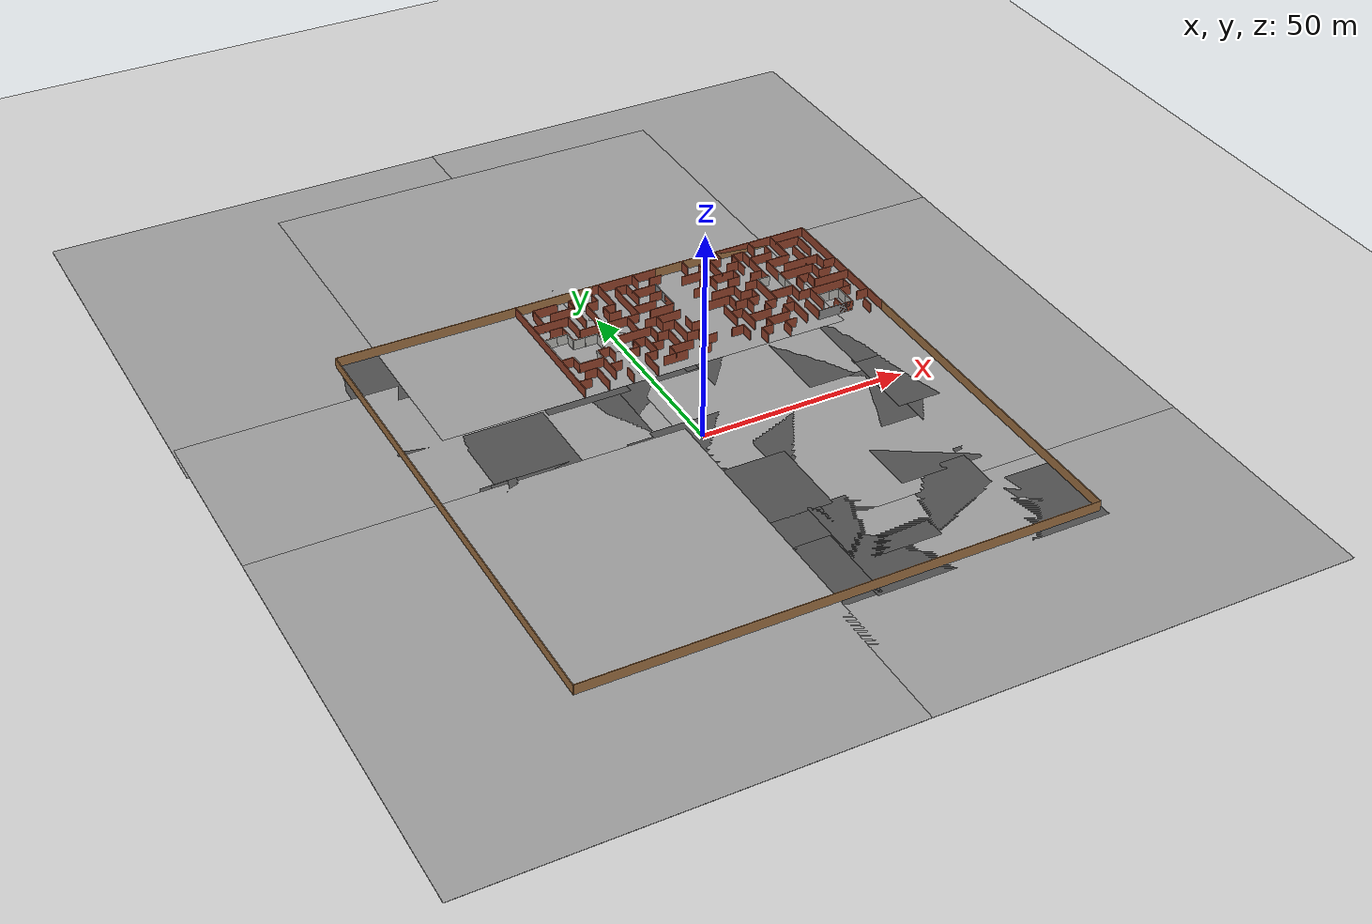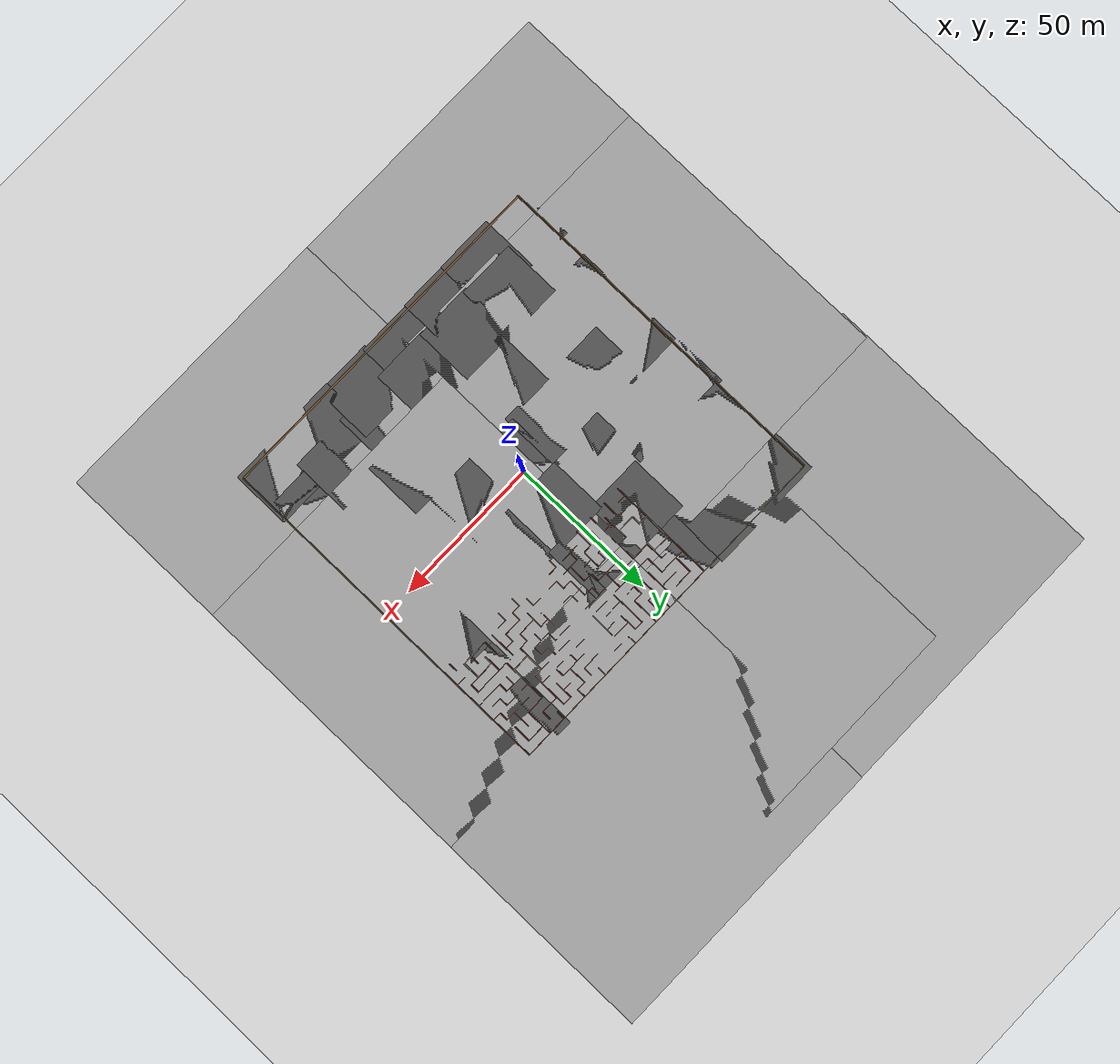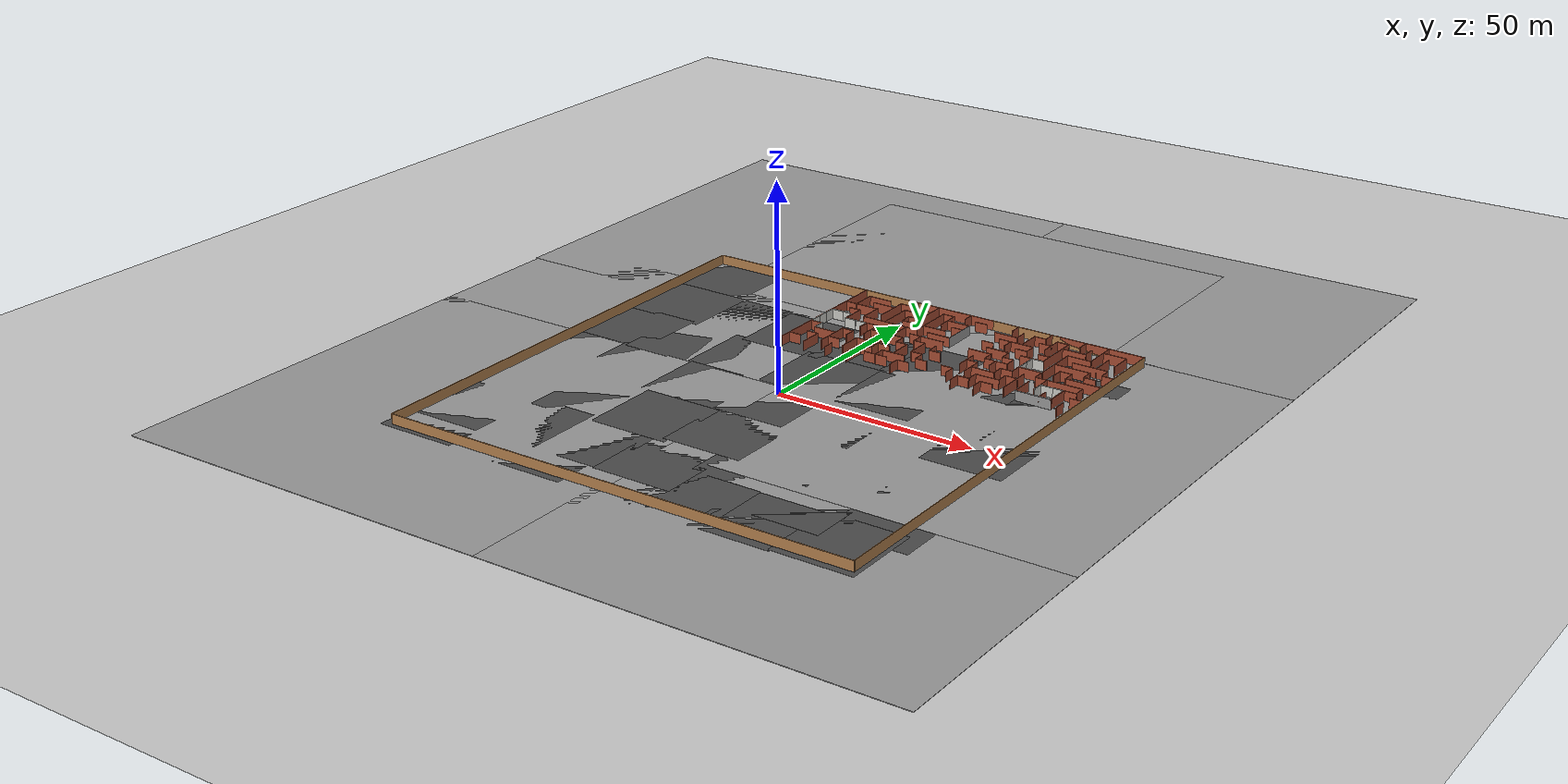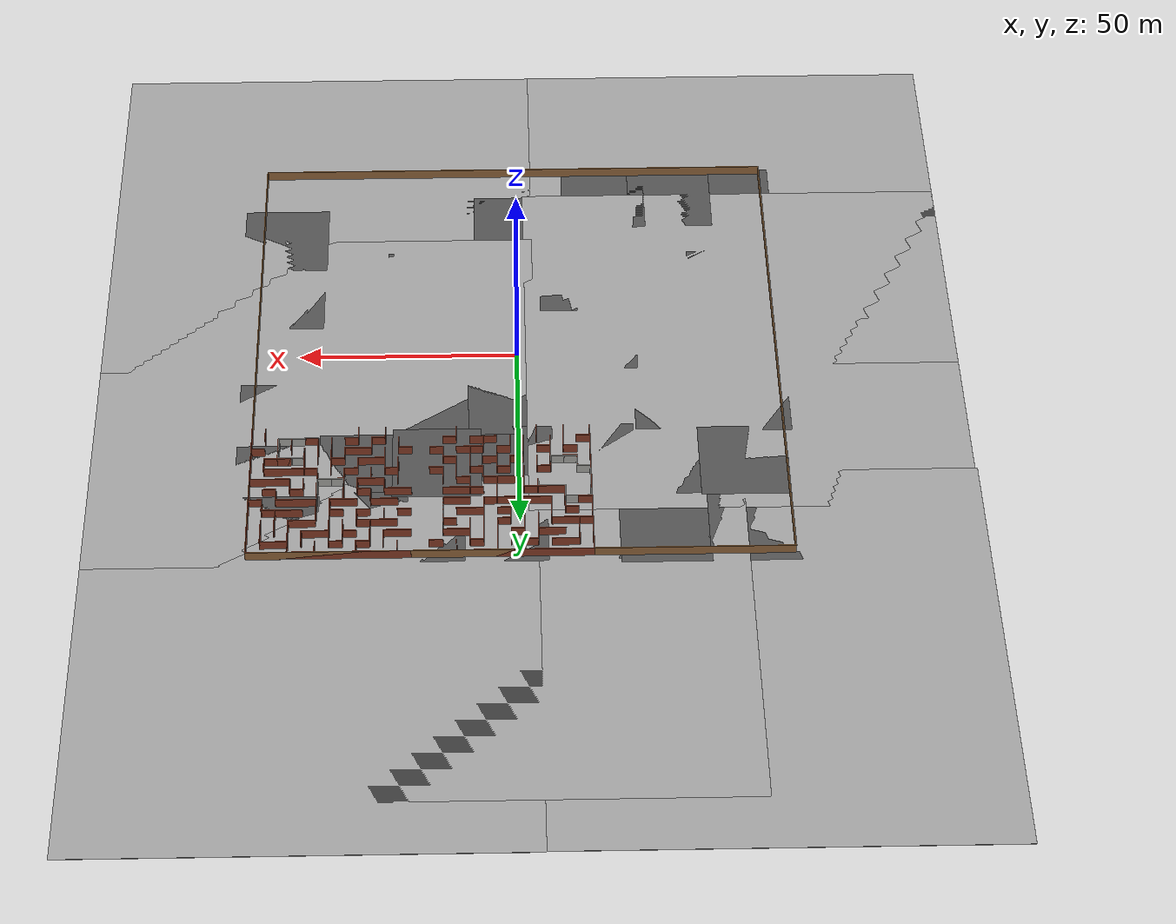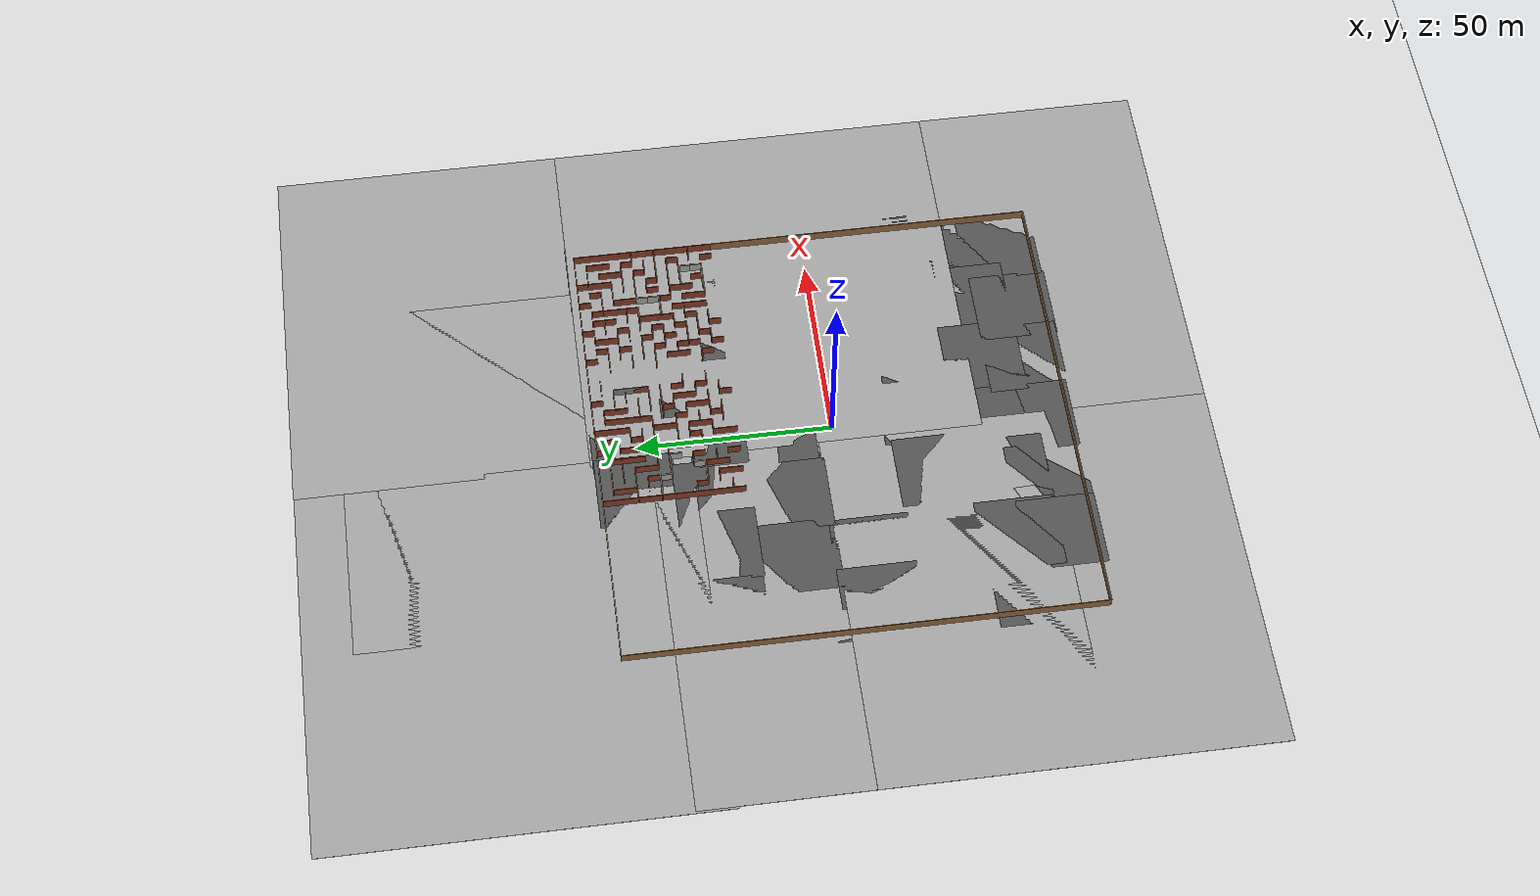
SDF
<sdf version="1.6">
 <world name="default">
  <light name="sun" type="directional">
   <pose>0 0 10 0 -0 0</pose>
   <diffuse>0.8 0.8 0.8 1</diffuse>
   <specular>0.2 0.2 0.2 1</specular>
   <attenuation>
    <range>1000</range>
    <constant>0.9</constant>
    <linear>0.01</linear>
    <quadratic>0.001</quadratic>
   </attenuation>
   <direction>-0.5 0.1 -0.9</direction>
  </light>
  <model name="ground_plane">
   <static>1</static>
   <link name="link">
    <collision name="collision">
     <geometry><plane><normal>0 0 1</normal><size>100 100</size></plane></geometry>
     <surface><friction><ode><mu>100</mu><mu2>50</mu2></ode></friction></surface>
    </collision>
    <visual name="visual">
     <cast_shadows>0</cast_shadows>
     <geometry><plane><normal>0 0 1</normal><size>100 100</size></plane></geometry>
     <material>
      <script><uri>file://media/materials/scripts/gazebo.material</uri><name>Gazebo/Grey</name></script>
     </material>
    </visual>
   </link>
  </model>
  <physics name="default_physics" default="0" type="ode">
   <max_step_size>0.001</max_step_size>
   <real_time_factor>1</real_time_factor>
   <real_time_update_rate>1000</real_time_update_rate>
  </physics>
  <scene><ambient>0.4 0.4 0.4 1</ambient><background>0.7 0.7 0.7 1</background><shadows>1</shadows></scene>
  <spherical_coordinates>
   <surface_model>EARTH_WGS84</surface_model>
   <latitude_deg>0</latitude_deg>
   <longitude_deg>0</longitude_deg>
   <elevation>0</elevation>
   <heading_deg>0</heading_deg>
  </spherical_coordinates>
  <model name="maze_final_2_0">
   <pose>42 42 0 0 -0 0</pose>
   <link name="Wall_10">
    <collision name="Wall_10_Collision">
     <geometry><box><size>3.15 0.15 2.5</size></box></geometry>
     <pose>0 0 1.25 0 -0 0</pose>
    </collision>
    <visual name="Wall_10_Visual">
     <pose>0 0 1.25 0 -0 0</pose>
     <geometry><box><size>3.15 0.15 2.5</size></box></geometry>
     <material>
      <script><uri>file://media/materials/scripts/gazebo.material</uri><name>Gazebo/Bricks</name></script>
      <ambient>1 1 1 1</ambient>
     </material>
    </visual>
    <pose>-16.5 -12 0 0 -0 0</pose>
   </link>
   <link name="Wall_100">
    <collision name="Wall_100_Collision">
     <geometry><box><size>3.15 0.15 2.5</size></box></geometry>
     <pose>0 0 1.25 0 -0 0</pose>
    </collision>
    <visual name="Wall_100_Visual">
     <pose>0 0 1.25 0 -0 0</pose>
     <geometry><box><size>3.15 0.15 2.5</size></box></geometry>
     <material>
      <script><uri>file://media/materials/scripts/gazebo.material</uri><name>Gazebo/Bricks</name></script>
      <ambient>1 1 1 1</ambient>
     </material>
    </visual>
    <pose>-4.5 12 0 0 -0 3.14159</pose>
   </link>
   <link name="Wall_102">
    <collision name="Wall_102_Collision">
     <geometry><box><size>9.15 0.15 2.5</size></box></geometry>
     <pose>0 0 1.25 0 -0 0</pose>
    </collision>
    <visual name="Wall_102_Visual">
     <pose>0 0 1.25 0 -0 0</pose>
     <geometry><box><size>9.15 0.15 2.5</size></box></geometry>
     <material>
      <script><uri>file://media/materials/scripts/gazebo.material</uri><name>Gazebo/Bricks</name></script>
      <ambient>1 1 1 1</ambient>
     </material>
    </visual>
    <pose>-0.0065 7.5 0 0 0 -1.57224</pose>
   </link>
   <link name="Wall_103">
    <collision name="Wall_103_Collision">
     <geometry><box><size>6.137 0.15 2.5</size></box></geometry>
     <pose>0 0 1.25 0 -0 0</pose>
    </collision>
    <visual name="Wall_103_Visual">
     <pose>0 0 1.25 0 -0 0</pose>
     <geometry><box><size>6.137 0.15 2.5</size></box></geometry>
     <material>
      <script><uri>file://media/materials/scripts/gazebo.material</uri><name>Gazebo/Bricks</name></script>
      <ambient>1 1 1 1</ambient>
     </material>
    </visual>
    <pose>-3.0065 3 0 0 -0 3.14159</pose>
   </link>
   <link name="Wall_105">
    <collision name="Wall_105_Collision">
     <geometry><box><size>3.15 0.15 2.5</size></box></geometry>
     <pose>0 0 1.25 0 -0 0</pose>
    </collision>
    <visual name="Wall_105_Visual">
     <pose>0 0 1.25 0 -0 0</pose>
     <geometry><box><size>3.15 0.15 2.5</size></box></geometry>
     <material>
      <script><uri>file://media/materials/scripts/gazebo.material</uri><name>Gazebo/Bricks</name></script>
      <ambient>1 1 1 1</ambient>
     </material>
    </visual>
    <pose>-1.5 6 0 0 -0 3.14159</pose>
   </link>
   <link name="Wall_108">
    <collision name="Wall_108_Collision">
     <geometry><box><size>6.15 0.15 2.5</size></box></geometry>
     <pose>0 0 1.25 0 -0 0</pose>
    </collision>
    <visual name="Wall_108_Visual">
     <pose>0 0 1.25 0 -0 0</pose>
     <geometry><box><size>6.15 0.15 2.5</size></box></geometry>
     <material>
      <script><uri>file://media/materials/scripts/gazebo.material</uri><name>Gazebo/Bricks</name></script>
      <ambient>1 1 1 1</ambient>
     </material>
    </visual>
    <pose>1e-06 -3 0 0 -0 3.14159</pose>
   </link>
   <link name="Wall_110">
    <collision name="Wall_110_Collision">
     <geometry><box><size>9.15 0.15 2.5</size></box></geometry>
     <pose>0 0 1.25 0 -0 0</pose>
    </collision>
    <visual name="Wall_110_Visual">
     <pose>0 0 1.25 0 -0 0</pose>
     <geometry><box><size>9.15 0.15 2.5</size></box></geometry>
     <material>
      <script><uri>file://media/materials/scripts/gazebo.material</uri><name>Gazebo/Bricks</name></script>
      <ambient>1 1 1 1</ambient>
     </material>
    </visual>
    <pose>-3 -1.5 0 0 -0 1.5708</pose>
   </link>
   <link name="Wall_112">
    <collision name="Wall_112_Collision">
     <geometry><box><size>3.15 0.15 2.5</size></box></geometry>
     <pose>0 0 1.25 0 -0 0</pose>
    </collision>
    <visual name="Wall_112_Visual">
     <pose>0 0 1.25 0 -0 0</pose>
     <geometry><box><size>3.15 0.15 2.5</size></box></geometry>
     <material>
      <script><uri>file://media/materials/scripts/gazebo.material</uri><name>Gazebo/Bricks</name></script>
      <ambient>1 1 1 1</ambient>
     </material>
    </visual>
    <pose>-4.5 -6 0 0 -0 3.14159</pose>
   </link>
   <link name="Wall_113">
    <collision name="Wall_113_Collision">
     <geometry><box><size>3.15 0.15 2.5</size></box></geometry>
     <pose>0 0 1.25 0 -0 0</pose>
    </collision>
    <visual name="Wall_113_Visual">
     <pose>0 0 1.25 0 -0 0</pose>
     <geometry><box><size>3.15 0.15 2.5</size></box></geometry>
     <material>
      <script><uri>file://media/materials/scripts/gazebo.material</uri><name>Gazebo/Bricks</name></script>
      <ambient>1 1 1 1</ambient>
     </material>
    </visual>
    <pose>-6 -7.5 0 0 0 -1.5708</pose>
   </link>
   <link name="Wall_114">
    <collision name="Wall_114_Collision">
     <geometry><box><size>6.15 0.15 2.5</size></box></geometry>
     <pose>0 0 1.25 0 -0 0</pose>
    </collision>
    <visual name="Wall_114_Visual">
     <pose>0 0 1.25 0 -0 0</pose>
     <geometry><box><size>6.15 0.15 2.5</size></box></geometry>
     <material>
      <script><uri>file://media/materials/scripts/gazebo.material</uri><name>Gazebo/Bricks</name></script>
      <ambient>1 1 1 1</ambient>
     </material>
    </visual>
    <pose>-9 -9 0 0 -0 3.14159</pose>
   </link>
   <link name="Wall_116">
    <collision name="Wall_116_Collision">
     <geometry><box><size>6.15 0.15 2.5</size></box></geometry>
     <pose>0 0 1.25 0 -0 0</pose>
    </collision>
    <visual name="Wall_116_Visual">
     <pose>0 0 1.25 0 -0 0</pose>
     <geometry><box><size>6.15 0.15 2.5</size></box></geometry>
     <material>
      <script><uri>file://media/materials/scripts/gazebo.material</uri><name>Gazebo/Bricks</name></script>
      <ambient>1 1 1 1</ambient>
     </material>
    </visual>
    <pose>-12 -9 0 0 -0 1.5708</pose>
   </link>
   <link name="Wall_117">
    <collision name="Wall_117_Collision">
     <geometry><box><size>3.15 0.15 2.5</size></box></geometry>
     <pose>0 0 1.25 0 -0 0</pose>
    </collision>
    <visual name="Wall_117_Visual">
     <pose>0 0 1.25 0 -0 0</pose>
     <geometry><box><size>3.15 0.15 2.5</size></box></geometry>
     <material>
      <script><uri>file://media/materials/scripts/gazebo.material</uri><name>Gazebo/Bricks</name></script>
      <ambient>1 1 1 1</ambient>
     </material>
    </visual>
    <pose>-13.5 -6 0 0 -0 3.14159</pose>
   </link>
   <link name="Wall_119">
    <collision name="Wall_119_Collision">
     <geometry><box><size>6.15 0.15 2.5</size></box></geometry>
     <pose>0 0 1.25 0 -0 0</pose>
    </collision>
    <visual name="Wall_119_Visual">
     <pose>0 0 1.25 0 -0 0</pose>
     <geometry><box><size>6.15 0.15 2.5</size></box></geometry>
     <material>
      <script><uri>file://media/materials/scripts/gazebo.material</uri><name>Gazebo/Bricks</name></script>
      <ambient>1 1 1 1</ambient>
     </material>
    </visual>
    <pose>-15 -6 0 0 0 -1.5708</pose>
   </link>
   <link name="Wall_12">
    <collision name="Wall_12_Collision">
     <geometry><box><size>6.15 0.15 2.5</size></box></geometry>
     <pose>0 0 1.25 0 -0 0</pose>
    </collision>
    <visual name="Wall_12_Visual">
     <pose>0 0 1.25 0 -0 0</pose>
     <geometry><box><size>6.15 0.15 2.5</size></box></geometry>
     <material>
      <script><uri>file://media/materials/scripts/gazebo.material</uri><name>Gazebo/Bricks</name></script>
      <ambient>1 1 1 1</ambient>
     </material>
    </visual>
    <pose>-15 -1e-06 0 0 -0 0</pose>
   </link>
   <link name="Wall_121">
    <collision name="Wall_121_Collision">
     <geometry><box><size>3.13703 0.15 2.5</size></box></geometry>
     <pose>0 0 1.25 0 -0 0</pose>
    </collision>
    <visual name="Wall_121_Visual">
     <pose>0 0 1.25 0 -0 0</pose>
     <geometry><box><size>3.13703 0.15 2.5</size></box></geometry>
     <material>
      <script><uri>file://media/materials/scripts/gazebo.material</uri><name>Gazebo/Bricks</name></script>
      <ambient>1 1 1 1</ambient>
     </material>
    </visual>
    <pose>-12.0065 -1.4935 0 0 0 -1.57515</pose>
   </link>
   <link name="Wall_122">
    <collision name="Wall_122_Collision">
     <geometry><box><size>6.16301 0.15 2.5</size></box></geometry>
     <pose>0 0 1.25 0 -0 0</pose>
    </collision>
    <visual name="Wall_122_Visual">
     <pose>0 0 1.25 0 -0 0</pose>
     <geometry><box><size>6.16301 0.15 2.5</size></box></geometry>
     <material>
      <script><uri>file://media/materials/scripts/gazebo.material</uri><name>Gazebo/Bricks</name></script>
      <ambient>1 1 1 1</ambient>
     </material>
    </visual>
    <pose>-9.0065 -2.9935 0 0 0 -0.002162</pose>
   </link>
   <link name="Wall_123">
    <collision name="Wall_123_Collision">
     <geometry><box><size>3.15 0.15 2.5</size></box></geometry>
     <pose>0 0 1.25 0 -0 0</pose>
    </collision>
    <visual name="Wall_123_Visual">
     <pose>0 0 1.25 0 -0 0</pose>
     <geometry><box><size>3.15 0.15 2.5</size></box></geometry>
     <material>
      <script><uri>file://media/materials/scripts/gazebo.material</uri><name>Gazebo/Bricks</name></script>
      <ambient>1 1 1 1</ambient>
     </material>
    </visual>
    <pose>-6 -1.5 0 0 -0 1.5708</pose>
   </link>
   <link name="Wall_124">
    <collision name="Wall_124_Collision">
     <geometry><box><size>3.15 0.15 2.5</size></box></geometry>
     <pose>0 0 1.25 0 -0 0</pose>
    </collision>
    <visual name="Wall_124_Visual">
     <pose>0 0 1.25 0 -0 0</pose>
     <geometry><box><size>3.15 0.15 2.5</size></box></geometry>
     <material>
      <script><uri>file://media/materials/scripts/gazebo.material</uri><name>Gazebo/Bricks</name></script>
      <ambient>1 1 1 1</ambient>
     </material>
    </visual>
    <pose>-7.5 -1e-06 0 0 -0 3.14159</pose>
   </link>
   <link name="Wall_125">
    <collision name="Wall_125_Collision">
     <geometry><box><size>3.15 0.15 2.5</size></box></geometry>
     <pose>0 0 1.25 0 -0 0</pose>
    </collision>
    <visual name="Wall_125_Visual">
     <pose>0 0 1.25 0 -0 0</pose>
     <geometry><box><size>3.15 0.15 2.5</size></box></geometry>
     <material>
      <script><uri>file://media/materials/scripts/gazebo.material</uri><name>Gazebo/Bricks</name></script>
      <ambient>1 1 1 1</ambient>
     </material>
    </visual>
    <pose>-9 1.5 0 0 -0 1.5708</pose>
   </link>
   <link name="Wall_127">
    <collision name="Wall_127_Collision">
     <geometry><box><size>6.15 0.15 2.5</size></box></geometry>
     <pose>0 0 1.25 0 -0 0</pose>
    </collision>
    <visual name="Wall_127_Visual">
     <pose>0 0 1.25 0 -0 0</pose>
     <geometry><box><size>6.15 0.15 2.5</size></box></geometry>
     <material>
      <script><uri>file://media/materials/scripts/gazebo.material</uri><name>Gazebo/Bricks</name></script>
      <ambient>1 1 1 1</ambient>
     </material>
    </visual>
    <pose>-12 3 0 0 -0 3.14159</pose>
   </link>
   <link name="Wall_129">
    <collision name="Wall_129_Collision">
     <geometry><box><size>3.15 0.15 2.5</size></box></geometry>
     <pose>0 0 1.25 0 -0 0</pose>
    </collision>
    <visual name="Wall_129_Visual">
     <pose>0 0 1.25 0 -0 0</pose>
     <geometry><box><size>3.15 0.15 2.5</size></box></geometry>
     <material>
      <script><uri>file://media/materials/scripts/gazebo.material</uri><name>Gazebo/Bricks</name></script>
      <ambient>1 1 1 1</ambient>
     </material>
    </visual>
    <pose>-9 -4.5 0 0 0 -1.5708</pose>
   </link>
   <link name="Wall_131">
    <collision name="Wall_131_Collision">
     <geometry><box><size>3.15 0.15 2.5</size></box></geometry>
     <pose>0 0 1.25 0 -0 0</pose>
    </collision>
    <visual name="Wall_131_Visual">
     <pose>0 0 1.25 0 -0 0</pose>
     <geometry><box><size>3.15 0.15 2.5</size></box></geometry>
     <material>
      <script><uri>file://media/materials/scripts/gazebo.material</uri><name>Gazebo/Bricks</name></script>
      <ambient>1 1 1 1</ambient>
     </material>
    </visual>
    <pose>-6 16.5 0 0 0 -1.5708</pose>
   </link>
   <link name="Wall_132">
    <collision name="Wall_132_Collision">
     <geometry><box><size>3.15 0.15 2.5</size></box></geometry>
     <pose>0 0 1.25 0 -0 0</pose>
    </collision>
    <visual name="Wall_132_Visual">
     <pose>0 0 1.25 0 -0 0</pose>
     <geometry><box><size>3.15 0.15 2.5</size></box></geometry>
     <material>
      <script><uri>file://media/materials/scripts/gazebo.material</uri><name>Gazebo/Bricks</name></script>
      <ambient>1 1 1 1</ambient>
     </material>
    </visual>
    <pose>-7.5 15 0 0 -0 3.14159</pose>
   </link>
   <link name="Wall_133">
    <collision name="Wall_133_Collision">
     <geometry><box><size>6.15 0.15 2.5</size></box></geometry>
     <pose>0 0 1.25 0 -0 0</pose>
    </collision>
    <visual name="Wall_133_Visual">
     <pose>0 0 1.25 0 -0 0</pose>
     <geometry><box><size>6.15 0.15 2.5</size></box></geometry>
     <material>
      <script><uri>file://media/materials/scripts/gazebo.material</uri><name>Gazebo/Bricks</name></script>
      <ambient>1 1 1 1</ambient>
     </material>
    </visual>
    <pose>-9 12 0 0 0 -1.5708</pose>
   </link>
   <link name="Wall_135">
    <collision name="Wall_135_Collision">
     <geometry><box><size>3.15 0.15 2.5</size></box></geometry>
     <pose>0 0 1.25 0 -0 0</pose>
    </collision>
    <visual name="Wall_135_Visual">
     <pose>0 0 1.25 0 -0 0</pose>
     <geometry><box><size>3.15 0.15 2.5</size></box></geometry>
     <material>
      <script><uri>file://media/materials/scripts/gazebo.material</uri><name>Gazebo/Bricks</name></script>
      <ambient>1 1 1 1</ambient>
     </material>
    </visual>
    <pose>-7.5 6 0 0 -0 0</pose>
   </link>
   <link name="Wall_136">
    <collision name="Wall_136_Collision">
     <geometry><box><size>3.15 0.15 2.5</size></box></geometry>
     <pose>0 0 1.25 0 -0 0</pose>
    </collision>
    <visual name="Wall_136_Visual">
     <pose>0 0 1.25 0 -0 0</pose>
     <geometry><box><size>3.15 0.15 2.5</size></box></geometry>
     <material>
      <script><uri>file://media/materials/scripts/gazebo.material</uri><name>Gazebo/Bricks</name></script>
      <ambient>1 1 1 1</ambient>
     </material>
    </visual>
    <pose>-6 7.5 0 0 -0 1.5708</pose>
   </link>
   <link name="Wall_137">
    <collision name="Wall_137_Collision">
     <geometry><box><size>9.15 0.15 2.5</size></box></geometry>
     <pose>0 0 1.25 0 -0 0</pose>
    </collision>
    <visual name="Wall_137_Visual">
     <pose>0 0 1.25 0 -0 0</pose>
     <geometry><box><size>9.15 0.15 2.5</size></box></geometry>
     <material>
      <script><uri>file://media/materials/scripts/gazebo.material</uri><name>Gazebo/Bricks</name></script>
      <ambient>1 1 1 1</ambient>
     </material>
    </visual>
    <pose>-10.5 9 0 0 -0 3.14159</pose>
   </link>
   <link name="Wall_139">
    <collision name="Wall_139_Collision">
     <geometry><box><size>3.15 0.15 2.5</size></box></geometry>
     <pose>0 0 1.25 0 -0 0</pose>
    </collision>
    <visual name="Wall_139_Visual">
     <pose>0 0 1.25 0 -0 0</pose>
     <geometry><box><size>3.15 0.15 2.5</size></box></geometry>
     <material>
      <script><uri>file://media/materials/scripts/gazebo.material</uri><name>Gazebo/Bricks</name></script>
      <ambient>1 1 1 1</ambient>
     </material>
    </visual>
    <pose>-12 7.5 0 0 0 -1.5708</pose>
   </link>
   <link name="Wall_14">
    <collision name="Wall_14_Collision">
     <geometry><box><size>3.15 0.15 2.5</size></box></geometry>
     <pose>0 0 1.25 0 -0 0</pose>
    </collision>
    <visual name="Wall_14_Visual">
     <pose>0 0 1.25 0 -0 0</pose>
     <geometry><box><size>3.15 0.15 2.5</size></box></geometry>
     <material>
      <script><uri>file://media/materials/scripts/gazebo.material</uri><name>Gazebo/Bricks</name></script>
      <ambient>1 1 1 1</ambient>
     </material>
    </visual>
    <pose>-16.5 6 0 0 -0 0</pose>
   </link>
   <link name="Wall_141">
    <collision name="Wall_141_Collision">
     <geometry><box><size>3.15 0.15 2.5</size></box></geometry>
     <pose>0 0 1.25 0 -0 0</pose>
    </collision>
    <visual name="Wall_141_Visual">
     <pose>0 0 1.25 0 -0 0</pose>
     <geometry><box><size>3.15 0.15 2.5</size></box></geometry>
     <material>
      <script><uri>file://media/materials/scripts/gazebo.material</uri><name>Gazebo/Bricks</name></script>
      <ambient>1 1 1 1</ambient>
     </material>
    </visual>
    <pose>-15 16.5 0 0 -0 1.5708</pose>
   </link>
   <link name="Wall_143">
    <collision name="Wall_143_Collision">
     <geometry><box><size>3.15 0.15 2.5</size></box></geometry>
     <pose>0 0 1.25 0 -0 0</pose>
    </collision>
    <visual name="Wall_143_Visual">
     <pose>0 0 1.25 0 -0 0</pose>
     <geometry><box><size>3.15 0.15 2.5</size></box></geometry>
     <material>
      <script><uri>file://media/materials/scripts/gazebo.material</uri><name>Gazebo/Bricks</name></script>
      <ambient>1 1 1 1</ambient>
     </material>
    </visual>
    <pose>-12 13.5 0 0 -0 1.5708</pose>
   </link>
   <link name="Wall_16">
    <collision name="Wall_16_Collision">
     <geometry><box><size>6.15 0.15 2.5</size></box></geometry>
     <pose>0 0 1.25 0 -0 0</pose>
    </collision>
    <visual name="Wall_16_Visual">
     <pose>0 0 1.25 0 -0 0</pose>
     <geometry><box><size>6.15 0.15 2.5</size></box></geometry>
     <material>
      <script><uri>file://media/materials/scripts/gazebo.material</uri><name>Gazebo/Bricks</name></script>
      <ambient>1 1 1 1</ambient>
     </material>
    </visual>
    <pose>-15 12 0 0 -0 0</pose>
   </link>
   <link name="Wall_18">
    <collision name="Wall_18_Collision">
     <geometry><box><size>3.15 0.15 2.5</size></box></geometry>
     <pose>0 0 1.25 0 -0 0</pose>
    </collision>
    <visual name="Wall_18_Visual">
     <pose>0 0 1.25 0 -0 0</pose>
     <geometry><box><size>3.15 0.15 2.5</size></box></geometry>
     <material>
      <script><uri>file://media/materials/scripts/gazebo.material</uri><name>Gazebo/Bricks</name></script>
      <ambient>1 1 1 1</ambient>
     </material>
    </visual>
    <pose>-12 -16.5 0 0 -0 1.5708</pose>
   </link>
   <link name="Wall_20">
    <collision name="Wall_20_Collision">
     <geometry><box><size>3.15 0.15 2.5</size></box></geometry>
     <pose>0 0 1.25 0 -0 0</pose>
    </collision>
    <visual name="Wall_20_Visual">
     <pose>0 0 1.25 0 -0 0</pose>
     <geometry><box><size>3.15 0.15 2.5</size></box></geometry>
     <material>
      <script><uri>file://media/materials/scripts/gazebo.material</uri><name>Gazebo/Bricks</name></script>
      <ambient>1 1 1 1</ambient>
     </material>
    </visual>
    <pose>-10.5 -15 0 0 -0 0</pose>
   </link>
   <link name="Wall_22">
    <collision name="Wall_22_Collision">
     <geometry><box><size>6.15 0.15 2.5</size></box></geometry>
     <pose>0 0 1.25 0 -0 0</pose>
    </collision>
    <visual name="Wall_22_Visual">
     <pose>0 0 1.25 0 -0 0</pose>
     <geometry><box><size>6.15 0.15 2.5</size></box></geometry>
     <material>
      <script><uri>file://media/materials/scripts/gazebo.material</uri><name>Gazebo/Bricks</name></script>
      <ambient>1 1 1 1</ambient>
     </material>
    </visual>
    <pose>-6 -12 0 0 -0 0</pose>
   </link>
   <link name="Wall_24">
    <collision name="Wall_24_Collision">
     <geometry><box><size>3.15 0.15 2.5</size></box></geometry>
     <pose>0 0 1.25 0 -0 0</pose>
    </collision>
    <visual name="Wall_24_Visual">
     <pose>0 0 1.25 0 -0 0</pose>
     <geometry><box><size>3.15 0.15 2.5</size></box></geometry>
     <material>
      <script><uri>file://media/materials/scripts/gazebo.material</uri><name>Gazebo/Bricks</name></script>
      <ambient>1 1 1 1</ambient>
     </material>
    </visual>
    <pose>-9 -13.5 0 0 0 -1.5708</pose>
   </link>
   <link name="Wall_26">
    <collision name="Wall_26_Collision">
     <geometry><box><size>3.15 0.15 2.5</size></box></geometry>
     <pose>0 0 1.25 0 -0 0</pose>
    </collision>
    <visual name="Wall_26_Visual">
     <pose>0 0 1.25 0 -0 0</pose>
     <geometry><box><size>3.15 0.15 2.5</size></box></geometry>
     <material>
      <script><uri>file://media/materials/scripts/gazebo.material</uri><name>Gazebo/Bricks</name></script>
      <ambient>1 1 1 1</ambient>
     </material>
    </visual>
    <pose>-6 -16.5 0 0 -0 1.5708</pose>
   </link>
   <link name="Wall_28">
    <collision name="Wall_28_Collision">
     <geometry><box><size>3.15 0.15 2.5</size></box></geometry>
     <pose>0 0 1.25 0 -0 0</pose>
    </collision>
    <visual name="Wall_28_Visual">
     <pose>0 0 1.25 0 -0 0</pose>
     <geometry><box><size>3.15 0.15 2.5</size></box></geometry>
     <material>
      <script><uri>file://media/materials/scripts/gazebo.material</uri><name>Gazebo/Bricks</name></script>
      <ambient>1 1 1 1</ambient>
     </material>
    </visual>
    <pose>-4.5 -15 0 0 -0 0</pose>
   </link>
   <link name="Wall_32">
    <collision name="Wall_32_Collision">
     <geometry><box><size>9.15 0.15 2.5</size></box></geometry>
     <pose>0 0 1.25 0 -0 0</pose>
    </collision>
    <visual name="Wall_32_Visual">
     <pose>0 0 1.25 0 -0 0</pose>
     <geometry><box><size>9.15 0.15 2.5</size></box></geometry>
     <material>
      <script><uri>file://media/materials/scripts/gazebo.material</uri><name>Gazebo/Bricks</name></script>
      <ambient>1 1 1 1</ambient>
     </material>
    </visual>
    <pose>1e-06 -10.5 0 0 -0 1.5708</pose>
   </link>
   <link name="Wall_34">
    <collision name="Wall_34_Collision">
     <geometry><box><size>3.15 0.15 2.5</size></box></geometry>
     <pose>0 0 1.25 0 -0 0</pose>
    </collision>
    <visual name="Wall_34_Visual">
     <pose>0 0 1.25 0 -0 0</pose>
     <geometry><box><size>3.15 0.15 2.5</size></box></geometry>
     <material>
      <script><uri>file://media/materials/scripts/gazebo.material</uri><name>Gazebo/Bricks</name></script>
      <ambient>1 1 1 1</ambient>
     </material>
    </visual>
    <pose>-1.5 -9 0 0 -0 3.14159</pose>
   </link>
   <link name="Wall_36">
    <collision name="Wall_36_Collision">
     <geometry><box><size>3.15 0.15 2.5</size></box></geometry>
     <pose>0 0 1.25 0 -0 0</pose>
    </collision>
    <visual name="Wall_36_Visual">
     <pose>0 0 1.25 0 -0 0</pose>
     <geometry><box><size>3.15 0.15 2.5</size></box></geometry>
     <material>
      <script><uri>file://media/materials/scripts/gazebo.material</uri><name>Gazebo/Bricks</name></script>
      <ambient>1 1 1 1</ambient>
     </material>
    </visual>
    <pose>-3 -10.5 0 0 -0 1.5708</pose>
   </link>
   <link name="Wall_4">
    <collision name="Wall_4_Collision">
     <geometry><box><size>36.15 0.15 2.5</size></box></geometry>
     <pose>0 0 1.25 0 -0 0</pose>
    </collision>
    <visual name="Wall_4_Visual">
     <pose>0 0 1.25 0 -0 0</pose>
     <geometry><box><size>36.15 0.15 2.5</size></box></geometry>
     <material>
      <script><uri>file://media/materials/scripts/gazebo.material</uri><name>Gazebo/Bricks</name></script>
      <ambient>1 1 1 1</ambient>
     </material>
    </visual>
    <pose>18 -1e-06 0 0 0 -1.5708</pose>
   </link>
   <link name="Wall_40">
    <collision name="Wall_40_Collision">
     <geometry><box><size>9.15 0.15 2.5</size></box></geometry>
     <pose>0 0 1.25 0 -0 0</pose>
    </collision>
    <visual name="Wall_40_Visual">
     <pose>0 0 1.25 0 -0 0</pose>
     <geometry><box><size>9.15 0.15 2.5</size></box></geometry>
     <material>
      <script><uri>file://media/materials/scripts/gazebo.material</uri><name>Gazebo/Grey</name></script>
      <ambient>1 1 1 1</ambient>
     </material>
    </visual>
    <pose>7.5 -15 0 0 -0 0</pose>
   </link>
   <link name="Wall_43">
    <collision name="Wall_43_Collision">
     <geometry><box><size>9.15 0.15 2.5</size></box></geometry>
     <pose>0 0 1.25 0 -0 0</pose>
    </collision>
    <visual name="Wall_43_Visual">
     <pose>0 0 1.25 0 -0 0</pose>
     <geometry><box><size>9.15 0.15 2.5</size></box></geometry>
     <material>
      <script><uri>file://media/materials/scripts/gazebo.material</uri><name>Gazebo/Bricks</name></script>
      <ambient>1 1 1 1</ambient>
     </material>
    </visual>
    <pose>9 13.5 0 0 0 -1.5708</pose>
   </link>
   <link name="Wall_45">
    <collision name="Wall_45_Collision">
     <geometry><box><size>6.15 0.15 2.5</size></box></geometry>
     <pose>0 0 1.25 0 -0 0</pose>
    </collision>
    <visual name="Wall_45_Visual">
     <pose>0 0 1.25 0 -0 0</pose>
     <geometry><box><size>6.15 0.15 2.5</size></box></geometry>
     <material>
      <script><uri>file://media/materials/scripts/gazebo.material</uri><name>Gazebo/Bricks</name></script>
      <ambient>1 1 1 1</ambient>
     </material>
    </visual>
    <pose>6 9 0 0 -0 3.14159</pose>
   </link>
   <link name="Wall_47">
    <collision name="Wall_47_Collision">
     <geometry><box><size>15.15 0.15 2.5</size></box></geometry>
     <pose>0 0 1.25 0 -0 0</pose>
    </collision>
    <visual name="Wall_47_Visual">
     <pose>0 0 1.25 0 -0 0</pose>
     <geometry><box><size>15.15 0.15 2.5</size></box></geometry>
     <material>
      <script><uri>file://media/materials/scripts/gazebo.material</uri><name>Gazebo/Bricks</name></script>
      <ambient>1 1 1 1</ambient>
     </material>
    </visual>
    <pose>3 1.5 0 0 0 -1.5708</pose>
   </link>
   <link name="Wall_49">
    <collision name="Wall_49_Collision">
     <geometry><box><size>12.15 0.15 2.5</size></box></geometry>
     <pose>0 0 1.25 0 -0 0</pose>
    </collision>
    <visual name="Wall_49_Visual">
     <pose>0 0 1.25 0 -0 0</pose>
     <geometry><box><size>12.15 0.15 2.5</size></box></geometry>
     <material>
      <script><uri>file://media/materials/scripts/gazebo.material</uri><name>Gazebo/Bricks</name></script>
      <ambient>1 1 1 1</ambient>
     </material>
    </visual>
    <pose>9 -6 0 0 -0 0</pose>
   </link>
   <link name="Wall_51">
    <collision name="Wall_51_Collision">
     <geometry><box><size>3.15 0.15 2.5</size></box></geometry>
     <pose>0 0 1.25 0 -0 0</pose>
    </collision>
    <visual name="Wall_51_Visual">
     <pose>0 0 1.25 0 -0 0</pose>
     <geometry><box><size>3.15 0.15 2.5</size></box></geometry>
     <material>
      <script><uri>file://media/materials/scripts/gazebo.material</uri><name>Gazebo/Bricks</name></script>
      <ambient>1 1 1 1</ambient>
     </material>
    </visual>
    <pose>15 -7.5 0 0 0 -1.5708</pose>
   </link>
   <link name="Wall_53">
    <collision name="Wall_53_Collision">
     <geometry><box><size>6.15 0.15 2.5</size></box></geometry>
     <pose>0 0 1.25 0 -0 0</pose>
    </collision>
    <visual name="Wall_53_Visual">
     <pose>0 0 1.25 0 -0 0</pose>
     <geometry><box><size>6.15 0.15 2.5</size></box></geometry>
     <material>
      <script><uri>file://media/materials/scripts/gazebo.material</uri><name>Gazebo/Bricks</name></script>
      <ambient>1 1 1 1</ambient>
     </material>
    </visual>
    <pose>12 -9 0 0 -0 3.14159</pose>
   </link>
   <link name="Wall_55">
    <collision name="Wall_55_Collision">
     <geometry><box><size>6.15 0.15 2.5</size></box></geometry>
     <pose>0 0 1.25 0 -0 0</pose>
    </collision>
    <visual name="Wall_55_Visual">
     <pose>0 0 1.25 0 -0 0</pose>
     <geometry><box><size>6.15 0.15 2.5</size></box></geometry>
     <material>
      <script><uri>file://media/materials/scripts/gazebo.material</uri><name>Gazebo/Bricks</name></script>
      <ambient>1 1 1 1</ambient>
     </material>
    </visual>
    <pose>12 -12 0 0 0 -1.5708</pose>
   </link>
   <link name="Wall_57">
    <collision name="Wall_57_Collision">
     <geometry><box><size>9.15 0.15 2.5</size></box></geometry>
     <pose>0 0 1.25 0 -0 0</pose>
    </collision>
    <visual name="Wall_57_Visual">
     <pose>0 0 1.25 0 -0 0</pose>
     <geometry><box><size>9.15 0.15 2.5</size></box></geometry>
     <material>
      <script><uri>file://media/materials/scripts/gazebo.material</uri><name>Gazebo/Bricks</name></script>
      <ambient>1 1 1 1</ambient>
     </material>
    </visual>
    <pose>7.5 -15 0 0 -0 3.14159</pose>
   </link>
   <link name="Wall_59">
    <collision name="Wall_59_Collision">
     <geometry><box><size>3.15 0.15 2.5</size></box></geometry>
     <pose>0 0 1.25 0 -0 0</pose>
    </collision>
    <visual name="Wall_59_Visual">
     <pose>0 0 1.25 0 -0 0</pose>
     <geometry><box><size>3.15 0.15 2.5</size></box></geometry>
     <material>
      <script><uri>file://media/materials/scripts/gazebo.material</uri><name>Gazebo/Bricks</name></script>
      <ambient>1 1 1 1</ambient>
     </material>
    </visual>
    <pose>9 -13.5 0 0 -0 1.5708</pose>
   </link>
   <link name="Wall_6">
    <collision name="Wall_6_Collision">
     <geometry><box><size>36.15 0.15 2.5</size></box></geometry>
     <pose>0 0 1.25 0 -0 0</pose>
    </collision>
    <visual name="Wall_6_Visual">
     <pose>0 0 1.25 0 -0 0</pose>
     <geometry><box><size>36.15 0.15 2.5</size></box></geometry>
     <material>
      <script><uri>file://media/materials/scripts/gazebo.material</uri><name>Gazebo/Bricks</name></script>
      <ambient>1 1 1 1</ambient>
     </material>
    </visual>
    <pose>1e-06 18 0 0 -0 3.14159</pose>
   </link>
   <link name="Wall_62">
    <collision name="Wall_62_Collision">
     <geometry><box><size>3.15 0.15 2.5</size></box></geometry>
     <pose>0 0 1.25 0 -0 0</pose>
    </collision>
    <visual name="Wall_62_Visual">
     <pose>0 0 1.25 0 -0 0</pose>
     <geometry><box><size>3.15 0.15 2.5</size></box></geometry>
     <material>
      <script><uri>file://media/materials/scripts/gazebo.material</uri><name>Gazebo/Bricks</name></script>
      <ambient>1 1 1 1</ambient>
     </material>
    </visual>
    <pose>10.5 -9 0 0 -0 3.14159</pose>
   </link>
   <link name="Wall_64">
    <collision name="Wall_64_Collision">
     <geometry><box><size>6.15 0.15 2.5</size></box></geometry>
     <pose>0 0 1.25 0 -0 0</pose>
    </collision>
    <visual name="Wall_64_Visual">
     <pose>0 0 1.25 0 -0 0</pose>
     <geometry><box><size>6.15 0.15 2.5</size></box></geometry>
     <material>
      <script><uri>file://media/materials/scripts/gazebo.material</uri><name>Gazebo/Bricks</name></script>
      <ambient>1 1 1 1</ambient>
     </material>
    </visual>
    <pose>3 -12 0 0 -0 1.5708</pose>
   </link>
   <link name="Wall_66">
    <collision name="Wall_66_Collision">
     <geometry><box><size>6.15 0.15 2.5</size></box></geometry>
     <pose>0 0 1.25 0 -0 0</pose>
    </collision>
    <visual name="Wall_66_Visual">
     <pose>0 0 1.25 0 -0 0</pose>
     <geometry><box><size>6.15 0.15 2.5</size></box></geometry>
     <material>
      <script><uri>file://media/materials/scripts/gazebo.material</uri><name>Gazebo/Bricks</name></script>
      <ambient>1 1 1 1</ambient>
     </material>
    </visual>
    <pose>6 -9 0 0 -0 1.5708</pose>
   </link>
   <link name="Wall_68">
    <collision name="Wall_68_Collision">
     <geometry><box><size>3.15 0.15 2.5</size></box></geometry>
     <pose>0 0 1.25 0 -0 0</pose>
    </collision>
    <visual name="Wall_68_Visual">
     <pose>0 0 1.25 0 -0 0</pose>
     <geometry><box><size>3.15 0.15 2.5</size></box></geometry>
     <material>
      <script><uri>file://media/materials/scripts/gazebo.material</uri><name>Gazebo/Bricks</name></script>
      <ambient>1 1 1 1</ambient>
     </material>
    </visual>
    <pose>16.5 -12 0 0 -0 3.14159</pose>
   </link>
   <link name="Wall_70">
    <collision name="Wall_70_Collision">
     <geometry><box><size>3.15 0.15 2.5</size></box></geometry>
     <pose>0 0 1.25 0 -0 0</pose>
    </collision>
    <visual name="Wall_70_Visual">
     <pose>0 0 1.25 0 -0 0</pose>
     <geometry><box><size>3.15 0.15 2.5</size></box></geometry>
     <material>
      <script><uri>file://media/materials/scripts/gazebo.material</uri><name>Gazebo/Bricks</name></script>
      <ambient>1 1 1 1</ambient>
     </material>
    </visual>
    <pose>15 -16.5 0 0 -0 1.5708</pose>
   </link>
   <link name="Wall_72">
    <collision name="Wall_72_Collision">
     <geometry><box><size>9.15 0.15 2.5</size></box></geometry>
     <pose>0 0 1.25 0 -0 0</pose>
    </collision>
    <visual name="Wall_72_Visual">
     <pose>0 0 1.25 0 -0 0</pose>
     <geometry><box><size>9.15 0.15 2.5</size></box></geometry>
     <material>
      <script><uri>file://media/materials/scripts/gazebo.material</uri><name>Gazebo/Bricks</name></script>
      <ambient>1 1 1 1</ambient>
     </material>
    </visual>
    <pose>13.5 -3 0 0 -0 3.14159</pose>
   </link>
   <link name="Wall_74">
    <collision name="Wall_74_Collision">
     <geometry><box><size>3.15 0.15 2.5</size></box></geometry>
     <pose>0 0 1.25 0 -0 0</pose>
    </collision>
    <visual name="Wall_74_Visual">
     <pose>0 0 1.25 0 -0 0</pose>
     <geometry><box><size>3.15 0.15 2.5</size></box></geometry>
     <material>
      <script><uri>file://media/materials/scripts/gazebo.material</uri><name>Gazebo/Bricks</name></script>
      <ambient>1 1 1 1</ambient>
     </material>
    </visual>
    <pose>9 -1.5 0 0 -0 1.5708</pose>
   </link>
   <link name="Wall_76">
    <collision name="Wall_76_Collision">
     <geometry><box><size>3.15 0.15 2.5</size></box></geometry>
     <pose>0 0 1.25 0 -0 0</pose>
    </collision>
    <visual name="Wall_76_Visual">
     <pose>0 0 1.25 0 -0 0</pose>
     <geometry><box><size>3.15 0.15 2.5</size></box></geometry>
     <material>
      <script><uri>file://media/materials/scripts/gazebo.material</uri><name>Gazebo/Bricks</name></script>
      <ambient>1 1 1 1</ambient>
     </material>
    </visual>
    <pose>7.5 -1e-06 0 0 -0 3.14159</pose>
   </link>
   <link name="Wall_77">
    <collision name="Wall_77_Collision">
     <geometry><box><size>3.15 0.15 2.5</size></box></geometry>
     <pose>0 0 1.25 0 -0 0</pose>
    </collision>
    <visual name="Wall_77_Visual">
     <pose>0 0 1.25 0 -0 0</pose>
     <geometry><box><size>3.15 0.15 2.5</size></box></geometry>
     <material>
      <script><uri>file://media/materials/scripts/gazebo.material</uri><name>Gazebo/Bricks</name></script>
      <ambient>1 1 1 1</ambient>
     </material>
    </visual>
    <pose>6 -1.5 0 0 0 -1.5708</pose>
   </link>
   <link name="Wall_79">
    <collision name="Wall_79_Collision">
     <geometry><box><size>3.15 0.15 2.5</size></box></geometry>
     <pose>0 0 1.25 0 -0 0</pose>
    </collision>
    <visual name="Wall_79_Visual">
     <pose>0 0 1.25 0 -0 0</pose>
     <geometry><box><size>3.15 0.15 2.5</size></box></geometry>
     <material>
      <script><uri>file://media/materials/scripts/gazebo.material</uri><name>Gazebo/Bricks</name></script>
      <ambient>1 1 1 1</ambient>
     </material>
    </visual>
    <pose>13.5 -1e-06 0 0 -0 3.14159</pose>
   </link>
   <link name="Wall_8">
    <collision name="Wall_8_Collision">
     <geometry><box><size>3.15 0.15 2.5</size></box></geometry>
     <pose>0 0 1.25 0 -0 0</pose>
    </collision>
    <visual name="Wall_8_Visual">
     <pose>0 0 1.25 0 -0 0</pose>
     <geometry><box><size>3.15 0.15 2.5</size></box></geometry>
     <material>
      <script><uri>file://media/materials/scripts/gazebo.material</uri><name>Gazebo/Bricks</name></script>
      <ambient>1 1 1 1</ambient>
     </material>
    </visual>
    <pose>-15 -13.5 0 0 -0 1.5708</pose>
   </link>
   <link name="Wall_80">
    <collision name="Wall_80_Collision">
     <geometry><box><size>3.15 0.15 2.5</size></box></geometry>
     <pose>0 0 1.25 0 -0 0</pose>
    </collision>
    <visual name="Wall_80_Visual">
     <pose>0 0 1.25 0 -0 0</pose>
     <geometry><box><size>3.15 0.15 2.5</size></box></geometry>
     <material>
      <script><uri>file://media/materials/scripts/gazebo.material</uri><name>Gazebo/Bricks</name></script>
      <ambient>1 1 1 1</ambient>
     </material>
    </visual>
    <pose>12 1.5 0 0 -0 1.5708</pose>
   </link>
   <link name="Wall_81">
    <collision name="Wall_81_Collision">
     <geometry><box><size>9.15 0.15 2.5</size></box></geometry>
     <pose>0 0 1.25 0 -0 0</pose>
    </collision>
    <visual name="Wall_81_Visual">
     <pose>0 0 1.25 0 -0 0</pose>
     <geometry><box><size>9.15 0.15 2.5</size></box></geometry>
     <material>
      <script><uri>file://media/materials/scripts/gazebo.material</uri><name>Gazebo/Bricks</name></script>
      <ambient>1 1 1 1</ambient>
     </material>
    </visual>
    <pose>7.5 3 0 0 -0 3.14159</pose>
   </link>
   <link name="Wall_83">
    <collision name="Wall_83_Collision">
     <geometry><box><size>3.15 0.15 2.5</size></box></geometry>
     <pose>0 0 1.25 0 -0 0</pose>
    </collision>
    <visual name="Wall_83_Visual">
     <pose>0 0 1.25 0 -0 0</pose>
     <geometry><box><size>3.15 0.15 2.5</size></box></geometry>
     <material>
      <script><uri>file://media/materials/scripts/gazebo.material</uri><name>Gazebo/Bricks</name></script>
      <ambient>1 1 1 1</ambient>
     </material>
    </visual>
    <pose>16.5 3 0 0 -0 3.14159</pose>
   </link>
   <link name="Wall_84">
    <collision name="Wall_84_Collision">
     <geometry><box><size>3.15 0.15 2.5</size></box></geometry>
     <pose>0 0 1.25 0 -0 0</pose>
    </collision>
    <visual name="Wall_84_Visual">
     <pose>0 0 1.25 0 -0 0</pose>
     <geometry><box><size>3.15 0.15 2.5</size></box></geometry>
     <material>
      <script><uri>file://media/materials/scripts/gazebo.material</uri><name>Gazebo/Bricks</name></script>
      <ambient>1 1 1 1</ambient>
     </material>
    </visual>
    <pose>15 4.5 0 0 -0 1.5708</pose>
   </link>
   <link name="Wall_85">
    <collision name="Wall_85_Collision">
     <geometry><box><size>9.15 0.15 2.5</size></box></geometry>
     <pose>0 0 1.25 0 -0 0</pose>
    </collision>
    <visual name="Wall_85_Visual">
     <pose>0 0 1.25 0 -0 0</pose>
     <geometry><box><size>9.15 0.15 2.5</size></box></geometry>
     <material>
      <script><uri>file://media/materials/scripts/gazebo.material</uri><name>Gazebo/Bricks</name></script>
      <ambient>1 1 1 1</ambient>
     </material>
    </visual>
    <pose>10.5 6 0 0 -0 3.14159</pose>
   </link>
   <link name="Wall_87">
    <collision name="Wall_87_Collision">
     <geometry><box><size>6.15 0.15 2.5</size></box></geometry>
     <pose>0 0 1.25 0 -0 0</pose>
    </collision>
    <visual name="Wall_87_Visual">
     <pose>0 0 1.25 0 -0 0</pose>
     <geometry><box><size>6.15 0.15 2.5</size></box></geometry>
     <material>
      <script><uri>file://media/materials/scripts/gazebo.material</uri><name>Gazebo/Bricks</name></script>
      <ambient>1 1 1 1</ambient>
     </material>
    </visual>
    <pose>15 12 0 0 -0 1.5708</pose>
   </link>
   <link name="Wall_88">
    <collision name="Wall_88_Collision">
     <geometry><box><size>6.15 0.15 2.5</size></box></geometry>
     <pose>0 0 1.25 0 -0 0</pose>
    </collision>
    <visual name="Wall_88_Visual">
     <pose>0 0 1.25 0 -0 0</pose>
     <geometry><box><size>6.15 0.15 2.5</size></box></geometry>
     <material>
      <script><uri>file://media/materials/scripts/gazebo.material</uri><name>Gazebo/Bricks</name></script>
      <ambient>1 1 1 1</ambient>
     </material>
    </visual>
    <pose>12 15 0 0 -0 3.14159</pose>
   </link>
   <link name="Wall_90">
    <collision name="Wall_90_Collision">
     <geometry><box><size>6.15 0.15 2.5</size></box></geometry>
     <pose>0 0 1.25 0 -0 0</pose>
    </collision>
    <visual name="Wall_90_Visual">
     <pose>0 0 1.25 0 -0 0</pose>
     <geometry><box><size>6.15 0.15 2.5</size></box></geometry>
     <material>
      <script><uri>file://media/materials/scripts/gazebo.material</uri><name>Gazebo/Bricks</name></script>
      <ambient>1 1 1 1</ambient>
     </material>
    </visual>
    <pose>12 9 0 0 0 -1.5708</pose>
   </link>
   <link name="Wall_92">
    <collision name="Wall_92_Collision">
     <geometry><box><size>3.15 0.15 2.5</size></box></geometry>
     <pose>0 0 1.25 0 -0 0</pose>
    </collision>
    <visual name="Wall_92_Visual">
     <pose>0 0 1.25 0 -0 0</pose>
     <geometry><box><size>3.15 0.15 2.5</size></box></geometry>
     <material>
      <script><uri>file://media/materials/scripts/gazebo.material</uri><name>Gazebo/Bricks</name></script>
      <ambient>1 1 1 1</ambient>
     </material>
    </visual>
    <pose>3 16.5 0 0 -0 1.5708</pose>
   </link>
   <link name="Wall_94">
    <collision name="Wall_94_Collision">
     <geometry><box><size>3.15 0.15 2.5</size></box></geometry>
     <pose>0 0 1.25 0 -0 0</pose>
    </collision>
    <visual name="Wall_94_Visual">
     <pose>0 0 1.25 0 -0 0</pose>
     <geometry><box><size>3.15 0.15 2.5</size></box></geometry>
     <material>
      <script><uri>file://media/materials/scripts/gazebo.material</uri><name>Gazebo/Bricks</name></script>
      <ambient>1 1 1 1</ambient>
     </material>
    </visual>
    <pose>6 13.5 0 0 0 -1.5708</pose>
   </link>
   <link name="Wall_95">
    <collision name="Wall_95_Collision">
     <geometry><box><size>6.15 0.15 2.5</size></box></geometry>
     <pose>0 0 1.25 0 -0 0</pose>
    </collision>
    <visual name="Wall_95_Visual">
     <pose>0 0 1.25 0 -0 0</pose>
     <geometry><box><size>6.15 0.15 2.5</size></box></geometry>
     <material>
      <script><uri>file://media/materials/scripts/gazebo.material</uri><name>Gazebo/Bricks</name></script>
      <ambient>1 1 1 1</ambient>
     </material>
    </visual>
    <pose>3 12 0 0 -0 3.14159</pose>
   </link>
   <link name="Wall_96">
    <collision name="Wall_96_Collision">
     <geometry><box><size>3.15 0.15 2.5</size></box></geometry>
     <pose>0 0 1.25 0 -0 0</pose>
    </collision>
    <visual name="Wall_96_Visual">
     <pose>0 0 1.25 0 -0 0</pose>
     <geometry><box><size>3.15 0.15 2.5</size></box></geometry>
     <material>
      <script><uri>file://media/materials/scripts/gazebo.material</uri><name>Gazebo/Bricks</name></script>
      <ambient>1 1 1 1</ambient>
     </material>
    </visual>
    <pose>1e-06 13.5 0 0 -0 1.5708</pose>
   </link>
   <link name="Wall_97">
    <collision name="Wall_97_Collision">
     <geometry><box><size>3.15 0.15 2.5</size></box></geometry>
     <pose>0 0 1.25 0 -0 0</pose>
    </collision>
    <visual name="Wall_97_Visual">
     <pose>0 0 1.25 0 -0 0</pose>
     <geometry><box><size>3.15 0.15 2.5</size></box></geometry>
     <material>
      <script><uri>file://media/materials/scripts/gazebo.material</uri><name>Gazebo/Bricks</name></script>
      <ambient>1 1 1 1</ambient>
     </material>
    </visual>
    <pose>-1.5 15 0 0 -0 3.14159</pose>
   </link>
   <link name="Wall_98">
    <collision name="Wall_98_Collision">
     <geometry><box><size>6.15 0.15 2.5</size></box></geometry>
     <pose>0 0 1.25 0 -0 0</pose>
    </collision>
    <visual name="Wall_98_Visual">
     <pose>0 0 1.25 0 -0 0</pose>
     <geometry><box><size>6.15 0.15 2.5</size></box></geometry>
     <material>
      <script><uri>file://media/materials/scripts/gazebo.material</uri><name>Gazebo/Bricks</name></script>
      <ambient>1 1 1 1</ambient>
     </material>
    </visual>
    <pose>-3 12 0 0 0 -1.5708</pose>
   </link>
   <static>1</static>
  </model>
  <model name="ground_plane_0">
   <static>1</static>
   <link name="link">
    <collision name="collision">
     <geometry><plane><normal>0 0 1</normal><size>100 100</size></plane></geometry>
     <surface><friction><ode><mu>100</mu><mu2>50</mu2></ode></friction></surface>
    </collision>
    <visual name="visual">
     <cast_shadows>0</cast_shadows>
     <geometry><plane><normal>0 0 1</normal><size>100 100</size></plane></geometry>
     <material>
      <script><uri>file://media/materials/scripts/gazebo.material</uri><name>Gazebo/Grey</name></script>
     </material>
    </visual>
   </link>
   <pose>0 74 0 0 -0 0</pose>
  </model>
  <model name="ground_plane_1">
   <static>1</static>
   <link name="link">
    <collision name="collision">
     <geometry><plane><normal>0 0 1</normal><size>100 100</size></plane></geometry>
     <surface><friction><ode><mu>100</mu><mu2>50</mu2></ode></friction></surface>
    </collision>
    <visual name="visual">
     <cast_shadows>0</cast_shadows>
     <geometry><plane><normal>0 0 1</normal><size>100 100</size></plane></geometry>
     <material>
      <script><uri>file://media/materials/scripts/gazebo.material</uri><name>Gazebo/Grey</name></script>
     </material>
    </visual>
   </link>
   <pose>46 86.5842 0 0 -0 0</pose>
  </model>
  <model name="ground_plane_2">
   <static>1</static>
   <link name="link">
    <collision name="collision">
     <geometry><plane><normal>0 0 1</normal><size>100 100</size></plane></geometry>
     <surface><friction><ode><mu>100</mu><mu2>50</mu2></ode></friction></surface>
    </collision>
    <visual name="visual">
     <cast_shadows>0</cast_shadows>
     <geometry><plane><normal>0 0 1</normal><size>100 100</size></plane></geometry>
     <material>
      <script><uri>file://media/materials/scripts/gazebo.material</uri><name>Gazebo/Grey</name></script>
     </material>
    </visual>
   </link>
   <pose>46 12 0 0 -0 0</pose>
  </model>
  <model name="ground_plane_3">
   <static>1</static>
   <link name="link">
    <collision name="collision">
     <geometry><plane><normal>0 0 1</normal><size>100 100</size></plane></geometry>
     <surface><friction><ode><mu>100</mu><mu2>50</mu2></ode></friction></surface>
    </collision>
    <visual name="visual">
     <cast_shadows>0</cast_shadows>
     <geometry><plane><normal>0 0 1</normal><size>100 100</size></plane></geometry>
     <material>
      <script><uri>file://media/materials/scripts/gazebo.material</uri><name>Gazebo/Grey</name></script>
     </material>
    </visual>
   </link>
   <pose>46 -46 0 0 -0 0</pose>
  </model>
  <model name="ground_plane_4">
   <static>1</static>
   <link name="link">
    <collision name="collision">
     <geometry><plane><normal>0 0 1</normal><size>100 100</size></plane></geometry>
     <surface><friction><ode><mu>100</mu><mu2>50</mu2></ode></friction></surface>
    </collision>
    <visual name="visual">
     <cast_shadows>0</cast_shadows>
     <geometry><plane><normal>0 0 1</normal><size>100 100</size></plane></geometry>
     <material>
      <script><uri>file://media/materials/scripts/gazebo.material</uri><name>Gazebo/Grey</name></script>
     </material>
    </visual>
   </link>
   <pose>-52.5239 86.437 0 0 -0 0</pose>
  </model>
  <model name="ground_plane_5">
   <static>1</static>
   <link name="link">
    <collision name="collision">
     <geometry><plane><normal>0 0 1</normal><size>100 100</size></plane></geometry>
     <surface><friction><ode><mu>100</mu><mu2>50</mu2></ode></friction></surface>
    </collision>
    <visual name="visual">
     <cast_shadows>0</cast_shadows>
     <geometry><plane><normal>0 0 1</normal><size>100 100</size></plane></geometry>
     <material>
      <script><uri>file://media/materials/scripts/gazebo.material</uri><name>Gazebo/Grey</name></script>
     </material>
    </visual>
   </link>
   <pose>-52 -3 0 0 -0 0</pose>
  </model>
  <model name="ground_plane_6">
   <static>1</static>
   <link name="link">
    <collision name="collision">
     <geometry><plane><normal>0 0 1</normal><size>100 100</size></plane></geometry>
     <surface><friction><ode><mu>100</mu><mu2>50</mu2></ode></friction></surface>
    </collision>
    <visual name="visual">
     <cast_shadows>0</cast_shadows>
     <geometry><plane><normal>0 0 1</normal><size>100 100</size></plane></geometry>
     <material>
      <script><uri>file://media/materials/scripts/gazebo.material</uri><name>Gazebo/Grey</name></script>
     </material>
    </visual>
   </link>
   <pose>-52 -46 0 0 -0 0</pose>
  </model>
  <model name="map_final_frame_1">
   <link name="Wall_0">
    <collision name="Wall_0_Collision">
     <geometry><box><size>120.15 0.15 2.5</size></box></geometry>
     <pose>0 0 1.25 0 -0 0</pose>
    </collision>
    <visual name="Wall_0_Visual">
     <pose>0 0 1.25 0 -0 0</pose>
     <geometry><box><size>120.15 0.15 2.5</size></box></geometry>
     <material>
      <script><uri>file://media/materials/scripts/gazebo.material</uri><name>Gazebo/Wood</name></script>
      <ambient>1 1 1 1</ambient>
     </material>
    </visual>
    <pose>0 60 0 0 -0 0</pose>
   </link>
   <link name="Wall_1">
    <collision name="Wall_1_Collision">
     <geometry><box><size>120.15 0.15 2.5</size></box></geometry>
     <pose>0 0 1.25 0 -0 0</pose>
    </collision>
    <visual name="Wall_1_Visual">
     <pose>0 0 1.25 0 -0 0</pose>
     <geometry><box><size>120.15 0.15 2.5</size></box></geometry>
     <material>
      <script><uri>file://media/materials/scripts/gazebo.material</uri><name>Gazebo/Wood</name></script>
      <ambient>1 1 1 1</ambient>
     </material>
    </visual>
    <pose>60 0 0 0 0 -1.5708</pose>
   </link>
   <link name="Wall_2">
    <collision name="Wall_2_Collision">
     <geometry><box><size>120.15 0.15 2.5</size></box></geometry>
     <pose>0 0 1.25 0 -0 0</pose>
    </collision>
    <visual name="Wall_2_Visual">
     <pose>0 0 1.25 0 -0 0</pose>
     <geometry><box><size>120.15 0.15 2.5</size></box></geometry>
     <material>
      <script><uri>file://media/materials/scripts/gazebo.material</uri><name>Gazebo/Wood</name></script>
      <ambient>1 1 1 1</ambient>
     </material>
    </visual>
    <pose>0 -60 0 0 -0 3.14159</pose>
   </link>
   <link name="Wall_3">
    <collision name="Wall_3_Collision">
     <geometry><box><size>120.15 0.15 2.5</size></box></geometry>
     <pose>0 0 1.25 0 -0 0</pose>
    </collision>
    <visual name="Wall_3_Visual">
     <pose>0 0 1.25 0 -0 0</pose>
     <geometry><box><size>120.15 0.15 2.5</size></box></geometry>
     <material>
      <script><uri>file://media/materials/scripts/gazebo.material</uri><name>Gazebo/Wood</name></script>
      <ambient>1 1 1 1</ambient>
     </material>
    </visual>
    <pose>-60 0 0 0 -0 1.5708</pose>
   </link>
   <static>1</static>
  </model>
  <gravity>0 0 -9.8</gravity>
  <magnetic_field>6e-06 2.3e-05 -4.2e-05</magnetic_field>
  <atmosphere type="adiabatic"/>
  <audio><device>default</device></audio>
  <model name="maze_final_2_0_clone">
   <pose>2 42 0 0 -0 1.57079</pose>
   <link name="Wall_10">
    <collision name="Wall_10_Collision">
     <geometry><box><size>3.15 0.15 2.5</size></box></geometry>
     <pose>0 0 1.25 0 -0 0</pose>
    </collision>
    <visual name="Wall_10_Visual">
     <pose>0 0 1.25 0 -0 0</pose>
     <geometry><box><size>3.15 0.15 2.5</size></box></geometry>
     <material>
      <script><uri>file://media/materials/scripts/gazebo.material</uri><name>Gazebo/Bricks</name></script>
      <ambient>1 1 1 1</ambient>
     </material>
    </visual>
    <pose>-16.5 -12 0 0 -0 0</pose>
   </link>
   <link name="Wall_102">
    <collision name="Wall_102_Collision">
     <geometry><box><size>9.15 0.15 2.5</size></box></geometry>
     <pose>0 0 1.25 0 -0 0</pose>
    </collision>
    <visual name="Wall_102_Visual">
     <pose>0 0 1.25 0 -0 0</pose>
     <geometry><box><size>9.15 0.15 2.5</size></box></geometry>
     <material>
      <script><uri>file://media/materials/scripts/gazebo.material</uri><name>Gazebo/Bricks</name></script>
      <ambient>1 1 1 1</ambient>
     </material>
    </visual>
    <pose>-0.0065 7.5 0 0 0 -1.57224</pose>
   </link>
   <link name="Wall_103">
    <collision name="Wall_103_Collision">
     <geometry><box><size>6.137 0.15 2.5</size></box></geometry>
     <pose>0 0 1.25 0 -0 0</pose>
    </collision>
    <visual name="Wall_103_Visual">
     <pose>0 0 1.25 0 -0 0</pose>
     <geometry><box><size>6.137 0.15 2.5</size></box></geometry>
     <material>
      <script><uri>file://media/materials/scripts/gazebo.material</uri><name>Gazebo/Bricks</name></script>
      <ambient>1 1 1 1</ambient>
     </material>
    </visual>
    <pose>-3.0065 3 0 0 -0 3.14159</pose>
   </link>
   <link name="Wall_105">
    <collision name="Wall_105_Collision">
     <geometry><box><size>3.15 0.15 2.5</size></box></geometry>
     <pose>0 0 1.25 0 -0 0</pose>
    </collision>
    <visual name="Wall_105_Visual">
     <pose>0 0 1.25 0 -0 0</pose>
     <geometry><box><size>3.15 0.15 2.5</size></box></geometry>
     <material>
      <script><uri>file://media/materials/scripts/gazebo.material</uri><name>Gazebo/Bricks</name></script>
      <ambient>1 1 1 1</ambient>
     </material>
    </visual>
    <pose>-1.5 6 0 0 -0 3.14159</pose>
   </link>
   <link name="Wall_108">
    <collision name="Wall_108_Collision">
     <geometry><box><size>6.15 0.15 2.5</size></box></geometry>
     <pose>0 0 1.25 0 -0 0</pose>
    </collision>
    <visual name="Wall_108_Visual">
     <pose>0 0 1.25 0 -0 0</pose>
     <geometry><box><size>6.15 0.15 2.5</size></box></geometry>
     <material>
      <script><uri>file://media/materials/scripts/gazebo.material</uri><name>Gazebo/Bricks</name></script>
      <ambient>1 1 1 1</ambient>
     </material>
    </visual>
    <pose>1e-06 -3 0 0 -0 3.14159</pose>
   </link>
   <link name="Wall_110">
    <collision name="Wall_110_Collision">
     <geometry><box><size>9.15 0.15 2.5</size></box></geometry>
     <pose>0 0 1.25 0 -0 0</pose>
    </collision>
    <visual name="Wall_110_Visual">
     <pose>0 0 1.25 0 -0 0</pose>
     <geometry><box><size>9.15 0.15 2.5</size></box></geometry>
     <material>
      <script><uri>file://media/materials/scripts/gazebo.material</uri><name>Gazebo/Bricks</name></script>
      <ambient>1 1 1 1</ambient>
     </material>
    </visual>
    <pose>-3 -1.5 0 0 -0 1.5708</pose>
   </link>
   <link name="Wall_112">
    <collision name="Wall_112_Collision">
     <geometry><box><size>3.15 0.15 2.5</size></box></geometry>
     <pose>0 0 1.25 0 -0 0</pose>
    </collision>
    <visual name="Wall_112_Visual">
     <pose>0 0 1.25 0 -0 0</pose>
     <geometry><box><size>3.15 0.15 2.5</size></box></geometry>
     <material>
      <script><uri>file://media/materials/scripts/gazebo.material</uri><name>Gazebo/Bricks</name></script>
      <ambient>1 1 1 1</ambient>
     </material>
    </visual>
    <pose>-4.5 -6 0 0 -0 3.14159</pose>
   </link>
   <link name="Wall_113">
    <collision name="Wall_113_Collision">
     <geometry><box><size>3.15 0.15 2.5</size></box></geometry>
     <pose>0 0 1.25 0 -0 0</pose>
    </collision>
    <visual name="Wall_113_Visual">
     <pose>0 0 1.25 0 -0 0</pose>
     <geometry><box><size>3.15 0.15 2.5</size></box></geometry>
     <material>
      <script><uri>file://media/materials/scripts/gazebo.material</uri><name>Gazebo/Bricks</name></script>
      <ambient>1 1 1 1</ambient>
     </material>
    </visual>
    <pose>-6 -7.5 0 0 0 -1.5708</pose>
   </link>
   <link name="Wall_114">
    <collision name="Wall_114_Collision">
     <geometry><box><size>6.15 0.15 2.5</size></box></geometry>
     <pose>0 0 1.25 0 -0 0</pose>
    </collision>
    <visual name="Wall_114_Visual">
     <pose>0 0 1.25 0 -0 0</pose>
     <geometry><box><size>6.15 0.15 2.5</size></box></geometry>
     <material>
      <script><uri>file://media/materials/scripts/gazebo.material</uri><name>Gazebo/Bricks</name></script>
      <ambient>1 1 1 1</ambient>
     </material>
    </visual>
    <pose>-9 -9 0 0 -0 3.14159</pose>
   </link>
   <link name="Wall_116">
    <collision name="Wall_116_Collision">
     <geometry><box><size>6.15 0.15 2.5</size></box></geometry>
     <pose>0 0 1.25 0 -0 0</pose>
    </collision>
    <visual name="Wall_116_Visual">
     <pose>0 0 1.25 0 -0 0</pose>
     <geometry><box><size>6.15 0.15 2.5</size></box></geometry>
     <material>
      <script><uri>file://media/materials/scripts/gazebo.material</uri><name>Gazebo/Bricks</name></script>
      <ambient>1 1 1 1</ambient>
     </material>
    </visual>
    <pose>-12 -9 0 0 -0 1.5708</pose>
   </link>
   <link name="Wall_117">
    <collision name="Wall_117_Collision">
     <geometry><box><size>3.15 0.15 2.5</size></box></geometry>
     <pose>0 0 1.25 0 -0 0</pose>
    </collision>
    <visual name="Wall_117_Visual">
     <pose>0 0 1.25 0 -0 0</pose>
     <geometry><box><size>3.15 0.15 2.5</size></box></geometry>
     <material>
      <script><uri>file://media/materials/scripts/gazebo.material</uri><name>Gazebo/Bricks</name></script>
      <ambient>1 1 1 1</ambient>
     </material>
    </visual>
    <pose>-13.5 -6 0 0 -0 3.14159</pose>
   </link>
   <link name="Wall_119">
    <collision name="Wall_119_Collision">
     <geometry><box><size>6.15 0.15 2.5</size></box></geometry>
     <pose>0 0 1.25 0 -0 0</pose>
    </collision>
    <visual name="Wall_119_Visual">
     <pose>0 0 1.25 0 -0 0</pose>
     <geometry><box><size>6.15 0.15 2.5</size></box></geometry>
     <material>
      <script><uri>file://media/materials/scripts/gazebo.material</uri><name>Gazebo/Bricks</name></script>
      <ambient>1 1 1 1</ambient>
     </material>
    </visual>
    <pose>-15 -6 0 0 0 -1.5708</pose>
   </link>
   <link name="Wall_12">
    <collision name="Wall_12_Collision">
     <geometry><box><size>6.15 0.15 2.5</size></box></geometry>
     <pose>0 0 1.25 0 -0 0</pose>
    </collision>
    <visual name="Wall_12_Visual">
     <pose>0 0 1.25 0 -0 0</pose>
     <geometry><box><size>6.15 0.15 2.5</size></box></geometry>
     <material>
      <script><uri>file://media/materials/scripts/gazebo.material</uri><name>Gazebo/Bricks</name></script>
      <ambient>1 1 1 1</ambient>
     </material>
    </visual>
    <pose>-15 -1e-06 0 0 -0 0</pose>
   </link>
   <link name="Wall_121">
    <collision name="Wall_121_Collision">
     <geometry><box><size>3.13703 0.15 2.5</size></box></geometry>
     <pose>0 0 1.25 0 -0 0</pose>
    </collision>
    <visual name="Wall_121_Visual">
     <pose>0 0 1.25 0 -0 0</pose>
     <geometry><box><size>3.13703 0.15 2.5</size></box></geometry>
     <material>
      <script><uri>file://media/materials/scripts/gazebo.material</uri><name>Gazebo/Bricks</name></script>
      <ambient>1 1 1 1</ambient>
     </material>
    </visual>
    <pose>-12.0065 -1.4935 0 0 0 -1.57515</pose>
   </link>
   <link name="Wall_122">
    <collision name="Wall_122_Collision">
     <geometry><box><size>6.16301 0.15 2.5</size></box></geometry>
     <pose>0 0 1.25 0 -0 0</pose>
    </collision>
    <visual name="Wall_122_Visual">
     <pose>0 0 1.25 0 -0 0</pose>
     <geometry><box><size>6.16301 0.15 2.5</size></box></geometry>
     <material>
      <script><uri>file://media/materials/scripts/gazebo.material</uri><name>Gazebo/Bricks</name></script>
      <ambient>1 1 1 1</ambient>
     </material>
    </visual>
    <pose>-9.0065 -2.9935 0 0 0 -0.002162</pose>
   </link>
   <link name="Wall_123">
    <collision name="Wall_123_Collision">
     <geometry><box><size>3.15 0.15 2.5</size></box></geometry>
     <pose>0 0 1.25 0 -0 0</pose>
    </collision>
    <visual name="Wall_123_Visual">
     <pose>0 0 1.25 0 -0 0</pose>
     <geometry><box><size>3.15 0.15 2.5</size></box></geometry>
     <material>
      <script><uri>file://media/materials/scripts/gazebo.material</uri><name>Gazebo/Bricks</name></script>
      <ambient>1 1 1 1</ambient>
     </material>
    </visual>
    <pose>-6 -1.5 0 0 -0 1.5708</pose>
   </link>
   <link name="Wall_124">
    <collision name="Wall_124_Collision">
     <geometry><box><size>3.15 0.15 2.5</size></box></geometry>
     <pose>0 0 1.25 0 -0 0</pose>
    </collision>
    <visual name="Wall_124_Visual">
     <pose>0 0 1.25 0 -0 0</pose>
     <geometry><box><size>3.15 0.15 2.5</size></box></geometry>
     <material>
      <script><uri>file://media/materials/scripts/gazebo.material</uri><name>Gazebo/Bricks</name></script>
      <ambient>1 1 1 1</ambient>
     </material>
    </visual>
    <pose>-7.5 -1e-06 0 0 -0 3.14159</pose>
   </link>
   <link name="Wall_125">
    <collision name="Wall_125_Collision">
     <geometry><box><size>3.15 0.15 2.5</size></box></geometry>
     <pose>0 0 1.25 0 -0 0</pose>
    </collision>
    <visual name="Wall_125_Visual">
     <pose>0 0 1.25 0 -0 0</pose>
     <geometry><box><size>3.15 0.15 2.5</size></box></geometry>
     <material>
      <script><uri>file://media/materials/scripts/gazebo.material</uri><name>Gazebo/Bricks</name></script>
      <ambient>1 1 1 1</ambient>
     </material>
    </visual>
    <pose>-9 1.5 0 0 -0 1.5708</pose>
   </link>
   <link name="Wall_127">
    <collision name="Wall_127_Collision">
     <geometry><box><size>6.15 0.15 2.5</size></box></geometry>
     <pose>0 0 1.25 0 -0 0</pose>
    </collision>
    <visual name="Wall_127_Visual">
     <pose>0 0 1.25 0 -0 0</pose>
     <geometry><box><size>6.15 0.15 2.5</size></box></geometry>
     <material>
      <script><uri>file://media/materials/scripts/gazebo.material</uri><name>Gazebo/Bricks</name></script>
      <ambient>1 1 1 1</ambient>
     </material>
    </visual>
    <pose>-12 3 0 0 -0 3.14159</pose>
   </link>
   <link name="Wall_129">
    <collision name="Wall_129_Collision">
     <geometry><box><size>3.15 0.15 2.5</size></box></geometry>
     <pose>0 0 1.25 0 -0 0</pose>
    </collision>
    <visual name="Wall_129_Visual">
     <pose>0 0 1.25 0 -0 0</pose>
     <geometry><box><size>3.15 0.15 2.5</size></box></geometry>
     <material>
      <script><uri>file://media/materials/scripts/gazebo.material</uri><name>Gazebo/Bricks</name></script>
      <ambient>1 1 1 1</ambient>
     </material>
    </visual>
    <pose>-9 -4.5 0 0 0 -1.5708</pose>
   </link>
   <link name="Wall_131">
    <collision name="Wall_131_Collision">
     <geometry><box><size>3.15 0.15 2.5</size></box></geometry>
     <pose>0 0 1.25 0 -0 0</pose>
    </collision>
    <visual name="Wall_131_Visual">
     <pose>0 0 1.25 0 -0 0</pose>
     <geometry><box><size>3.15 0.15 2.5</size></box></geometry>
     <material>
      <script><uri>file://media/materials/scripts/gazebo.material</uri><name>Gazebo/Bricks</name></script>
      <ambient>1 1 1 1</ambient>
     </material>
    </visual>
    <pose>-6 16.5 0 0 0 -1.5708</pose>
   </link>
   <link name="Wall_132">
    <collision name="Wall_132_Collision">
     <geometry><box><size>3.15 0.15 2.5</size></box></geometry>
     <pose>0 0 1.25 0 -0 0</pose>
    </collision>
    <visual name="Wall_132_Visual">
     <pose>0 0 1.25 0 -0 0</pose>
     <geometry><box><size>3.15 0.15 2.5</size></box></geometry>
     <material>
      <script><uri>file://media/materials/scripts/gazebo.material</uri><name>Gazebo/Bricks</name></script>
      <ambient>1 1 1 1</ambient>
     </material>
    </visual>
    <pose>-7.5 15 0 0 -0 3.14159</pose>
   </link>
   <link name="Wall_133">
    <collision name="Wall_133_Collision">
     <geometry><box><size>6.15 0.15 2.5</size></box></geometry>
     <pose>0 0 1.25 0 -0 0</pose>
    </collision>
    <visual name="Wall_133_Visual">
     <pose>0 0 1.25 0 -0 0</pose>
     <geometry><box><size>6.15 0.15 2.5</size></box></geometry>
     <material>
      <script><uri>file://media/materials/scripts/gazebo.material</uri><name>Gazebo/Bricks</name></script>
      <ambient>1 1 1 1</ambient>
     </material>
    </visual>
    <pose>-9 12 0 0 0 -1.5708</pose>
   </link>
   <link name="Wall_135">
    <collision name="Wall_135_Collision">
     <geometry><box><size>3.15 0.15 2.5</size></box></geometry>
     <pose>0 0 1.25 0 -0 0</pose>
    </collision>
    <visual name="Wall_135_Visual">
     <pose>0 0 1.25 0 -0 0</pose>
     <geometry><box><size>3.15 0.15 2.5</size></box></geometry>
     <material>
      <script><uri>file://media/materials/scripts/gazebo.material</uri><name>Gazebo/Bricks</name></script>
      <ambient>1 1 1 1</ambient>
     </material>
    </visual>
    <pose>-7.5 6 0 0 -0 0</pose>
   </link>
   <link name="Wall_136">
    <collision name="Wall_136_Collision">
     <geometry><box><size>3.15 0.15 2.5</size></box></geometry>
     <pose>0 0 1.25 0 -0 0</pose>
    </collision>
    <visual name="Wall_136_Visual">
     <pose>0 0 1.25 0 -0 0</pose>
     <geometry><box><size>3.15 0.15 2.5</size></box></geometry>
     <material>
      <script><uri>file://media/materials/scripts/gazebo.material</uri><name>Gazebo/Bricks</name></script>
      <ambient>1 1 1 1</ambient>
     </material>
    </visual>
    <pose>-6 7.5 0 0 -0 1.5708</pose>
   </link>
   <link name="Wall_137">
    <collision name="Wall_137_Collision">
     <geometry><box><size>9.15 0.15 2.5</size></box></geometry>
     <pose>0 0 1.25 0 -0 0</pose>
    </collision>
    <visual name="Wall_137_Visual">
     <pose>0 0 1.25 0 -0 0</pose>
     <geometry><box><size>9.15 0.15 2.5</size></box></geometry>
     <material>
      <script><uri>file://media/materials/scripts/gazebo.material</uri><name>Gazebo/Bricks</name></script>
      <ambient>1 1 1 1</ambient>
     </material>
    </visual>
    <pose>-10.5 9 0 0 -0 3.14159</pose>
   </link>
   <link name="Wall_139">
    <collision name="Wall_139_Collision">
     <geometry><box><size>3.15 0.15 2.5</size></box></geometry>
     <pose>0 0 1.25 0 -0 0</pose>
    </collision>
    <visual name="Wall_139_Visual">
     <pose>0 0 1.25 0 -0 0</pose>
     <geometry><box><size>3.15 0.15 2.5</size></box></geometry>
     <material>
      <script><uri>file://media/materials/scripts/gazebo.material</uri><name>Gazebo/Bricks</name></script>
      <ambient>1 1 1 1</ambient>
     </material>
    </visual>
    <pose>-12 7.5 0 0 0 -1.5708</pose>
   </link>
   <link name="Wall_14">
    <collision name="Wall_14_Collision">
     <geometry><box><size>3.15 0.15 2.5</size></box></geometry>
     <pose>0 0 1.25 0 -0 0</pose>
    </collision>
    <visual name="Wall_14_Visual">
     <pose>0 0 1.25 0 -0 0</pose>
     <geometry><box><size>3.15 0.15 2.5</size></box></geometry>
     <material>
      <script><uri>file://media/materials/scripts/gazebo.material</uri><name>Gazebo/Bricks</name></script>
      <ambient>1 1 1 1</ambient>
     </material>
    </visual>
    <pose>-16.5 6 0 0 -0 0</pose>
   </link>
   <link name="Wall_141">
    <collision name="Wall_141_Collision">
     <geometry><box><size>3.15 0.15 2.5</size></box></geometry>
     <pose>0 0 1.25 0 -0 0</pose>
    </collision>
    <visual name="Wall_141_Visual">
     <pose>0 0 1.25 0 -0 0</pose>
     <geometry><box><size>3.15 0.15 2.5</size></box></geometry>
     <material>
      <script><uri>file://media/materials/scripts/gazebo.material</uri><name>Gazebo/Bricks</name></script>
      <ambient>1 1 1 1</ambient>
     </material>
    </visual>
    <pose>-15 16.5 0 0 -0 1.5708</pose>
   </link>
   <link name="Wall_143">
    <collision name="Wall_143_Collision">
     <geometry><box><size>3.15 0.15 2.5</size></box></geometry>
     <pose>0 0 1.25 0 -0 0</pose>
    </collision>
    <visual name="Wall_143_Visual">
     <pose>0 0 1.25 0 -0 0</pose>
     <geometry><box><size>3.15 0.15 2.5</size></box></geometry>
     <material>
      <script><uri>file://media/materials/scripts/gazebo.material</uri><name>Gazebo/Bricks</name></script>
      <ambient>1 1 1 1</ambient>
     </material>
    </visual>
    <pose>-12 13.5 0 0 -0 1.5708</pose>
   </link>
   <link name="Wall_16">
    <collision name="Wall_16_Collision">
     <geometry><box><size>6.15 0.15 2.5</size></box></geometry>
     <pose>0 0 1.25 0 -0 0</pose>
    </collision>
    <visual name="Wall_16_Visual">
     <pose>0 0 1.25 0 -0 0</pose>
     <geometry><box><size>6.15 0.15 2.5</size></box></geometry>
     <material>
      <script><uri>file://media/materials/scripts/gazebo.material</uri><name>Gazebo/Bricks</name></script>
      <ambient>1 1 1 1</ambient>
     </material>
    </visual>
    <pose>-15 12 0 0 -0 0</pose>
   </link>
   <link name="Wall_18">
    <collision name="Wall_18_Collision">
     <geometry><box><size>3.15 0.15 2.5</size></box></geometry>
     <pose>0 0 1.25 0 -0 0</pose>
    </collision>
    <visual name="Wall_18_Visual">
     <pose>0 0 1.25 0 -0 0</pose>
     <geometry><box><size>3.15 0.15 2.5</size></box></geometry>
     <material>
      <script><uri>file://media/materials/scripts/gazebo.material</uri><name>Gazebo/Bricks</name></script>
      <ambient>1 1 1 1</ambient>
     </material>
    </visual>
    <pose>-12 -16.5 0 0 -0 1.5708</pose>
   </link>
   <link name="Wall_20">
    <collision name="Wall_20_Collision">
     <geometry><box><size>3.15 0.15 2.5</size></box></geometry>
     <pose>0 0 1.25 0 -0 0</pose>
    </collision>
    <visual name="Wall_20_Visual">
     <pose>0 0 1.25 0 -0 0</pose>
     <geometry><box><size>3.15 0.15 2.5</size></box></geometry>
     <material>
      <script><uri>file://media/materials/scripts/gazebo.material</uri><name>Gazebo/Bricks</name></script>
      <ambient>1 1 1 1</ambient>
     </material>
    </visual>
    <pose>-10.5 -15 0 0 -0 0</pose>
   </link>
   <link name="Wall_22">
    <collision name="Wall_22_Collision">
     <geometry><box><size>6.15 0.15 2.5</size></box></geometry>
     <pose>0 0 1.25 0 -0 0</pose>
    </collision>
    <visual name="Wall_22_Visual">
     <pose>0 0 1.25 0 -0 0</pose>
     <geometry><box><size>6.15 0.15 2.5</size></box></geometry>
     <material>
      <script><uri>file://media/materials/scripts/gazebo.material</uri><name>Gazebo/Bricks</name></script>
      <ambient>1 1 1 1</ambient>
     </material>
    </visual>
    <pose>-6 -12 0 0 -0 0</pose>
   </link>
   <link name="Wall_24">
    <collision name="Wall_24_Collision">
     <geometry><box><size>3.15 0.15 2.5</size></box></geometry>
     <pose>0 0 1.25 0 -0 0</pose>
    </collision>
    <visual name="Wall_24_Visual">
     <pose>0 0 1.25 0 -0 0</pose>
     <geometry><box><size>3.15 0.15 2.5</size></box></geometry>
     <material>
      <script><uri>file://media/materials/scripts/gazebo.material</uri><name>Gazebo/Bricks</name></script>
      <ambient>1 1 1 1</ambient>
     </material>
    </visual>
    <pose>-9 -13.5 0 0 0 -1.5708</pose>
   </link>
   <link name="Wall_26">
    <collision name="Wall_26_Collision">
     <geometry><box><size>3.15 0.15 2.5</size></box></geometry>
     <pose>0 0 1.25 0 -0 0</pose>
    </collision>
    <visual name="Wall_26_Visual">
     <pose>0 0 1.25 0 -0 0</pose>
     <geometry><box><size>3.15 0.15 2.5</size></box></geometry>
     <material>
      <script><uri>file://media/materials/scripts/gazebo.material</uri><name>Gazebo/Bricks</name></script>
      <ambient>1 1 1 1</ambient>
     </material>
    </visual>
    <pose>-6 -16.5 0 0 -0 1.5708</pose>
   </link>
   <link name="Wall_28">
    <collision name="Wall_28_Collision">
     <geometry><box><size>3.15 0.15 2.5</size></box></geometry>
     <pose>0 0 1.25 0 -0 0</pose>
    </collision>
    <visual name="Wall_28_Visual">
     <pose>0 0 1.25 0 -0 0</pose>
     <geometry><box><size>3.15 0.15 2.5</size></box></geometry>
     <material>
      <script><uri>file://media/materials/scripts/gazebo.material</uri><name>Gazebo/Bricks</name></script>
      <ambient>1 1 1 1</ambient>
     </material>
    </visual>
    <pose>-4.5 -15 0 0 -0 0</pose>
   </link>
   <link name="Wall_32">
    <collision name="Wall_32_Collision">
     <geometry><box><size>9.15 0.15 2.5</size></box></geometry>
     <pose>0 0 1.25 0 -0 0</pose>
    </collision>
    <visual name="Wall_32_Visual">
     <pose>0 0 1.25 0 -0 0</pose>
     <geometry><box><size>9.15 0.15 2.5</size></box></geometry>
     <material>
      <script><uri>file://media/materials/scripts/gazebo.material</uri><name>Gazebo/Bricks</name></script>
      <ambient>1 1 1 1</ambient>
     </material>
    </visual>
    <pose>1e-06 -10.5 0 0 -0 1.5708</pose>
   </link>
   <link name="Wall_34">
    <collision name="Wall_34_Collision">
     <geometry><box><size>3.15 0.15 2.5</size></box></geometry>
     <pose>0 0 1.25 0 -0 0</pose>
    </collision>
    <visual name="Wall_34_Visual">
     <pose>0 0 1.25 0 -0 0</pose>
     <geometry><box><size>3.15 0.15 2.5</size></box></geometry>
     <material>
      <script><uri>file://media/materials/scripts/gazebo.material</uri><name>Gazebo/Bricks</name></script>
      <ambient>1 1 1 1</ambient>
     </material>
    </visual>
    <pose>-1.5 -9 0 0 -0 3.14159</pose>
   </link>
   <link name="Wall_36">
    <collision name="Wall_36_Collision">
     <geometry><box><size>3.15 0.15 2.5</size></box></geometry>
     <pose>0 0 1.25 0 -0 0</pose>
    </collision>
    <visual name="Wall_36_Visual">
     <pose>0 0 1.25 0 -0 0</pose>
     <geometry><box><size>3.15 0.15 2.5</size></box></geometry>
     <material>
      <script><uri>file://media/materials/scripts/gazebo.material</uri><name>Gazebo/Bricks</name></script>
      <ambient>1 1 1 1</ambient>
     </material>
    </visual>
    <pose>-3 -10.5 0 0 -0 1.5708</pose>
   </link>
   <link name="Wall_4">
    <collision name="Wall_4_Collision">
     <geometry><box><size>36.15 0.15 2.5</size></box></geometry>
     <pose>0 0 1.25 0 -0 0</pose>
    </collision>
    <visual name="Wall_4_Visual">
     <pose>0 0 1.25 0 -0 0</pose>
     <geometry><box><size>36.15 0.15 2.5</size></box></geometry>
     <material>
      <script><uri>file://media/materials/scripts/gazebo.material</uri><name>Gazebo/Bricks</name></script>
      <ambient>1 1 1 1</ambient>
     </material>
    </visual>
    <pose>18 -1e-06 0 0 0 -1.5708</pose>
   </link>
   <link name="Wall_40">
    <collision name="Wall_40_Collision">
     <geometry><box><size>9.15 0.15 2.5</size></box></geometry>
     <pose>0 0 1.25 0 -0 0</pose>
    </collision>
    <visual name="Wall_40_Visual">
     <pose>0 0 1.25 0 -0 0</pose>
     <geometry><box><size>9.15 0.15 2.5</size></box></geometry>
     <material>
      <script><uri>file://media/materials/scripts/gazebo.material</uri><name>Gazebo/Grey</name></script>
      <ambient>1 1 1 1</ambient>
     </material>
    </visual>
    <pose>7.5 -15 0 0 -0 0</pose>
   </link>
   <link name="Wall_43">
    <collision name="Wall_43_Collision">
     <geometry><box><size>9.15 0.15 2.5</size></box></geometry>
     <pose>0 0 1.25 0 -0 0</pose>
    </collision>
    <visual name="Wall_43_Visual">
     <pose>0 0 1.25 0 -0 0</pose>
     <geometry><box><size>9.15 0.15 2.5</size></box></geometry>
     <material>
      <script><uri>file://media/materials/scripts/gazebo.material</uri><name>Gazebo/Bricks</name></script>
      <ambient>1 1 1 1</ambient>
     </material>
    </visual>
    <pose>9 13.5 0 0 0 -1.5708</pose>
   </link>
   <link name="Wall_45">
    <collision name="Wall_45_Collision">
     <geometry><box><size>6.15 0.15 2.5</size></box></geometry>
     <pose>0 0 1.25 0 -0 0</pose>
    </collision>
    <visual name="Wall_45_Visual">
     <pose>0 0 1.25 0 -0 0</pose>
     <geometry><box><size>6.15 0.15 2.5</size></box></geometry>
     <material>
      <script><uri>file://media/materials/scripts/gazebo.material</uri><name>Gazebo/Bricks</name></script>
      <ambient>1 1 1 1</ambient>
     </material>
    </visual>
    <pose>6 9 0 0 -0 3.14159</pose>
   </link>
   <link name="Wall_47">
    <collision name="Wall_47_Collision">
     <geometry><box><size>15.15 0.15 2.5</size></box></geometry>
     <pose>0 0 1.25 0 -0 0</pose>
    </collision>
    <visual name="Wall_47_Visual">
     <pose>0 0 1.25 0 -0 0</pose>
     <geometry><box><size>15.15 0.15 2.5</size></box></geometry>
     <material>
      <script><uri>file://media/materials/scripts/gazebo.material</uri><name>Gazebo/Bricks</name></script>
      <ambient>1 1 1 1</ambient>
     </material>
    </visual>
    <pose>3 1.5 0 0 0 -1.5708</pose>
   </link>
   <link name="Wall_49">
    <collision name="Wall_49_Collision">
     <geometry><box><size>12.15 0.15 2.5</size></box></geometry>
     <pose>0 0 1.25 0 -0 0</pose>
    </collision>
    <visual name="Wall_49_Visual">
     <pose>0 0 1.25 0 -0 0</pose>
     <geometry><box><size>12.15 0.15 2.5</size></box></geometry>
     <material>
      <script><uri>file://media/materials/scripts/gazebo.material</uri><name>Gazebo/Bricks</name></script>
      <ambient>1 1 1 1</ambient>
     </material>
    </visual>
    <pose>9 -6 0 0 -0 0</pose>
   </link>
   <link name="Wall_51">
    <collision name="Wall_51_Collision">
     <geometry><box><size>3.15 0.15 2.5</size></box></geometry>
     <pose>0 0 1.25 0 -0 0</pose>
    </collision>
    <visual name="Wall_51_Visual">
     <pose>0 0 1.25 0 -0 0</pose>
     <geometry><box><size>3.15 0.15 2.5</size></box></geometry>
     <material>
      <script><uri>file://media/materials/scripts/gazebo.material</uri><name>Gazebo/Bricks</name></script>
      <ambient>1 1 1 1</ambient>
     </material>
    </visual>
    <pose>15 -7.5 0 0 0 -1.5708</pose>
   </link>
   <link name="Wall_53">
    <collision name="Wall_53_Collision">
     <geometry><box><size>6.15 0.15 2.5</size></box></geometry>
     <pose>0 0 1.25 0 -0 0</pose>
    </collision>
    <visual name="Wall_53_Visual">
     <pose>0 0 1.25 0 -0 0</pose>
     <geometry><box><size>6.15 0.15 2.5</size></box></geometry>
     <material>
      <script><uri>file://media/materials/scripts/gazebo.material</uri><name>Gazebo/Bricks</name></script>
      <ambient>1 1 1 1</ambient>
     </material>
    </visual>
    <pose>12 -9 0 0 -0 3.14159</pose>
   </link>
   <link name="Wall_55">
    <collision name="Wall_55_Collision">
     <geometry><box><size>6.15 0.15 2.5</size></box></geometry>
     <pose>0 0 1.25 0 -0 0</pose>
    </collision>
    <visual name="Wall_55_Visual">
     <pose>0 0 1.25 0 -0 0</pose>
     <geometry><box><size>6.15 0.15 2.5</size></box></geometry>
     <material>
      <script><uri>file://media/materials/scripts/gazebo.material</uri><name>Gazebo/Bricks</name></script>
      <ambient>1 1 1 1</ambient>
     </material>
    </visual>
    <pose>12 -12 0 0 0 -1.5708</pose>
   </link>
   <link name="Wall_57">
    <collision name="Wall_57_Collision">
     <geometry><box><size>9.15 0.15 2.5</size></box></geometry>
     <pose>0 0 1.25 0 -0 0</pose>
    </collision>
    <visual name="Wall_57_Visual">
     <pose>0 0 1.25 0 -0 0</pose>
     <geometry><box><size>9.15 0.15 2.5</size></box></geometry>
     <material>
      <script><uri>file://media/materials/scripts/gazebo.material</uri><name>Gazebo/Bricks</name></script>
      <ambient>1 1 1 1</ambient>
     </material>
    </visual>
    <pose>7.5 -15 0 0 -0 3.14159</pose>
   </link>
   <link name="Wall_59">
    <collision name="Wall_59_Collision">
     <geometry><box><size>3.15 0.15 2.5</size></box></geometry>
     <pose>0 0 1.25 0 -0 0</pose>
    </collision>
    <visual name="Wall_59_Visual">
     <pose>0 0 1.25 0 -0 0</pose>
     <geometry><box><size>3.15 0.15 2.5</size></box></geometry>
     <material>
      <script><uri>file://media/materials/scripts/gazebo.material</uri><name>Gazebo/Bricks</name></script>
      <ambient>1 1 1 1</ambient>
     </material>
    </visual>
    <pose>9 -13.5 0 0 -0 1.5708</pose>
   </link>
   <link name="Wall_6">
    <collision name="Wall_6_Collision">
     <geometry><box><size>36.15 0.15 2.5</size></box></geometry>
     <pose>0 0 1.25 0 -0 0</pose>
    </collision>
    <visual name="Wall_6_Visual">
     <pose>0 0 1.25 0 -0 0</pose>
     <geometry><box><size>36.15 0.15 2.5</size></box></geometry>
     <material>
      <script><uri>file://media/materials/scripts/gazebo.material</uri><name>Gazebo/Bricks</name></script>
      <ambient>1 1 1 1</ambient>
     </material>
    </visual>
    <pose>1e-06 18 0 0 -0 3.14159</pose>
   </link>
   <link name="Wall_62">
    <collision name="Wall_62_Collision">
     <geometry><box><size>3.15 0.15 2.5</size></box></geometry>
     <pose>0 0 1.25 0 -0 0</pose>
    </collision>
    <visual name="Wall_62_Visual">
     <pose>0 0 1.25 0 -0 0</pose>
     <geometry><box><size>3.15 0.15 2.5</size></box></geometry>
     <material>
      <script><uri>file://media/materials/scripts/gazebo.material</uri><name>Gazebo/Bricks</name></script>
      <ambient>1 1 1 1</ambient>
     </material>
    </visual>
    <pose>10.5 -9 0 0 -0 3.14159</pose>
   </link>
   <link name="Wall_64">
    <collision name="Wall_64_Collision">
     <geometry><box><size>6.15 0.15 2.5</size></box></geometry>
     <pose>0 0 1.25 0 -0 0</pose>
    </collision>
    <visual name="Wall_64_Visual">
     <pose>0 0 1.25 0 -0 0</pose>
     <geometry><box><size>6.15 0.15 2.5</size></box></geometry>
     <material>
      <script><uri>file://media/materials/scripts/gazebo.material</uri><name>Gazebo/Bricks</name></script>
      <ambient>1 1 1 1</ambient>
     </material>
    </visual>
    <pose>3 -12 0 0 -0 1.5708</pose>
   </link>
   <link name="Wall_66">
    <collision name="Wall_66_Collision">
     <geometry><box><size>6.15 0.15 2.5</size></box></geometry>
     <pose>0 0 1.25 0 -0 0</pose>
    </collision>
    <visual name="Wall_66_Visual">
     <pose>0 0 1.25 0 -0 0</pose>
     <geometry><box><size>6.15 0.15 2.5</size></box></geometry>
     <material>
      <script><uri>file://media/materials/scripts/gazebo.material</uri><name>Gazebo/Bricks</name></script>
      <ambient>1 1 1 1</ambient>
     </material>
    </visual>
    <pose>6 -9 0 0 -0 1.5708</pose>
   </link>
   <link name="Wall_68">
    <collision name="Wall_68_Collision">
     <geometry><box><size>3.15 0.15 2.5</size></box></geometry>
     <pose>0 0 1.25 0 -0 0</pose>
    </collision>
    <visual name="Wall_68_Visual">
     <pose>0 0 1.25 0 -0 0</pose>
     <geometry><box><size>3.15 0.15 2.5</size></box></geometry>
     <material>
      <script><uri>file://media/materials/scripts/gazebo.material</uri><name>Gazebo/Bricks</name></script>
      <ambient>1 1 1 1</ambient>
     </material>
    </visual>
    <pose>16.5 -12 0 0 -0 3.14159</pose>
   </link>
   <link name="Wall_70">
    <collision name="Wall_70_Collision">
     <geometry><box><size>3.15 0.15 2.5</size></box></geometry>
     <pose>0 0 1.25 0 -0 0</pose>
    </collision>
    <visual name="Wall_70_Visual">
     <pose>0 0 1.25 0 -0 0</pose>
     <geometry><box><size>3.15 0.15 2.5</size></box></geometry>
     <material>
      <script><uri>file://media/materials/scripts/gazebo.material</uri><name>Gazebo/Bricks</name></script>
      <ambient>1 1 1 1</ambient>
     </material>
    </visual>
    <pose>15 -16.5 0 0 -0 1.5708</pose>
   </link>
   <link name="Wall_72">
    <collision name="Wall_72_Collision">
     <geometry><box><size>9.15 0.15 2.5</size></box></geometry>
     <pose>0 0 1.25 0 -0 0</pose>
    </collision>
    <visual name="Wall_72_Visual">
     <pose>0 0 1.25 0 -0 0</pose>
     <geometry><box><size>9.15 0.15 2.5</size></box></geometry>
     <material>
      <script><uri>file://media/materials/scripts/gazebo.material</uri><name>Gazebo/Bricks</name></script>
      <ambient>1 1 1 1</ambient>
     </material>
    </visual>
    <pose>13.5 -3 0 0 -0 3.14159</pose>
   </link>
   <link name="Wall_74">
    <collision name="Wall_74_Collision">
     <geometry><box><size>3.15 0.15 2.5</size></box></geometry>
     <pose>0 0 1.25 0 -0 0</pose>
    </collision>
    <visual name="Wall_74_Visual">
     <pose>0 0 1.25 0 -0 0</pose>
     <geometry><box><size>3.15 0.15 2.5</size></box></geometry>
     <material>
      <script><uri>file://media/materials/scripts/gazebo.material</uri><name>Gazebo/Bricks</name></script>
      <ambient>1 1 1 1</ambient>
     </material>
    </visual>
    <pose>9 -1.5 0 0 -0 1.5708</pose>
   </link>
   <link name="Wall_76">
    <collision name="Wall_76_Collision">
     <geometry><box><size>3.15 0.15 2.5</size></box></geometry>
     <pose>0 0 1.25 0 -0 0</pose>
    </collision>
    <visual name="Wall_76_Visual">
     <pose>0 0 1.25 0 -0 0</pose>
     <geometry><box><size>3.15 0.15 2.5</size></box></geometry>
     <material>
      <script><uri>file://media/materials/scripts/gazebo.material</uri><name>Gazebo/Bricks</name></script>
      <ambient>1 1 1 1</ambient>
     </material>
    </visual>
    <pose>7.5 -1e-06 0 0 -0 3.14159</pose>
   </link>
   <link name="Wall_77">
    <collision name="Wall_77_Collision">
     <geometry><box><size>3.15 0.15 2.5</size></box></geometry>
     <pose>0 0 1.25 0 -0 0</pose>
    </collision>
    <visual name="Wall_77_Visual">
     <pose>0 0 1.25 0 -0 0</pose>
     <geometry><box><size>3.15 0.15 2.5</size></box></geometry>
     <material>
      <script><uri>file://media/materials/scripts/gazebo.material</uri><name>Gazebo/Bricks</name></script>
      <ambient>1 1 1 1</ambient>
     </material>
    </visual>
    <pose>6 -1.5 0 0 0 -1.5708</pose>
   </link>
   <link name="Wall_79">
    <collision name="Wall_79_Collision">
     <geometry><box><size>3.15 0.15 2.5</size></box></geometry>
     <pose>0 0 1.25 0 -0 0</pose>
    </collision>
    <visual name="Wall_79_Visual">
     <pose>0 0 1.25 0 -0 0</pose>
     <geometry><box><size>3.15 0.15 2.5</size></box></geometry>
     <material>
      <script><uri>file://media/materials/scripts/gazebo.material</uri><name>Gazebo/Bricks</name></script>
      <ambient>1 1 1 1</ambient>
     </material>
    </visual>
    <pose>13.5 -1e-06 0 0 -0 3.14159</pose>
   </link>
   <link name="Wall_8">
    <collision name="Wall_8_Collision">
     <geometry><box><size>3.15 0.15 2.5</size></box></geometry>
     <pose>0 0 1.25 0 -0 0</pose>
    </collision>
    <visual name="Wall_8_Visual">
     <pose>0 0 1.25 0 -0 0</pose>
     <geometry><box><size>3.15 0.15 2.5</size></box></geometry>
     <material>
      <script><uri>file://media/materials/scripts/gazebo.material</uri><name>Gazebo/Bricks</name></script>
      <ambient>1 1 1 1</ambient>
     </material>
    </visual>
    <pose>-15 -13.5 0 0 -0 1.5708</pose>
   </link>
   <link name="Wall_80">
    <collision name="Wall_80_Collision">
     <geometry><box><size>3.15 0.15 2.5</size></box></geometry>
     <pose>0 0 1.25 0 -0 0</pose>
    </collision>
    <visual name="Wall_80_Visual">
     <pose>0 0 1.25 0 -0 0</pose>
     <geometry><box><size>3.15 0.15 2.5</size></box></geometry>
     <material>
      <script><uri>file://media/materials/scripts/gazebo.material</uri><name>Gazebo/Bricks</name></script>
      <ambient>1 1 1 1</ambient>
     </material>
    </visual>
    <pose>12 1.5 0 0 -0 1.5708</pose>
   </link>
   <link name="Wall_81">
    <collision name="Wall_81_Collision">
     <geometry><box><size>9.15 0.15 2.5</size></box></geometry>
     <pose>0 0 1.25 0 -0 0</pose>
    </collision>
    <visual name="Wall_81_Visual">
     <pose>0 0 1.25 0 -0 0</pose>
     <geometry><box><size>9.15 0.15 2.5</size></box></geometry>
     <material>
      <script><uri>file://media/materials/scripts/gazebo.material</uri><name>Gazebo/Bricks</name></script>
      <ambient>1 1 1 1</ambient>
     </material>
    </visual>
    <pose>7.5 3 0 0 -0 3.14159</pose>
   </link>
   <link name="Wall_83">
    <collision name="Wall_83_Collision">
     <geometry><box><size>3.15 0.15 2.5</size></box></geometry>
     <pose>0 0 1.25 0 -0 0</pose>
    </collision>
    <visual name="Wall_83_Visual">
     <pose>0 0 1.25 0 -0 0</pose>
     <geometry><box><size>3.15 0.15 2.5</size></box></geometry>
     <material>
      <script><uri>file://media/materials/scripts/gazebo.material</uri><name>Gazebo/Bricks</name></script>
      <ambient>1 1 1 1</ambient>
     </material>
    </visual>
    <pose>16.5 3 0 0 -0 3.14159</pose>
   </link>
   <link name="Wall_84">
    <collision name="Wall_84_Collision">
     <geometry><box><size>3.15 0.15 2.5</size></box></geometry>
     <pose>0 0 1.25 0 -0 0</pose>
    </collision>
    <visual name="Wall_84_Visual">
     <pose>0 0 1.25 0 -0 0</pose>
     <geometry><box><size>3.15 0.15 2.5</size></box></geometry>
     <material>
      <script><uri>file://media/materials/scripts/gazebo.material</uri><name>Gazebo/Bricks</name></script>
      <ambient>1 1 1 1</ambient>
     </material>
    </visual>
    <pose>15 4.5 0 0 -0 1.5708</pose>
   </link>
   <link name="Wall_85">
    <collision name="Wall_85_Collision">
     <geometry><box><size>9.15 0.15 2.5</size></box></geometry>
     <pose>0 0 1.25 0 -0 0</pose>
    </collision>
    <visual name="Wall_85_Visual">
     <pose>0 0 1.25 0 -0 0</pose>
     <geometry><box><size>9.15 0.15 2.5</size></box></geometry>
     <material>
      <script><uri>file://media/materials/scripts/gazebo.material</uri><name>Gazebo/Bricks</name></script>
      <ambient>1 1 1 1</ambient>
     </material>
    </visual>
    <pose>10.5 6 0 0 -0 3.14159</pose>
   </link>
   <link name="Wall_87">
    <collision name="Wall_87_Collision">
     <geometry><box><size>6.15 0.15 2.5</size></box></geometry>
     <pose>0 0 1.25 0 -0 0</pose>
    </collision>
    <visual name="Wall_87_Visual">
     <pose>0 0 1.25 0 -0 0</pose>
     <geometry><box><size>6.15 0.15 2.5</size></box></geometry>
     <material>
      <script><uri>file://media/materials/scripts/gazebo.material</uri><name>Gazebo/Bricks</name></script>
      <ambient>1 1 1 1</ambient>
     </material>
    </visual>
    <pose>15 12 0 0 -0 1.5708</pose>
   </link>
   <link name="Wall_88">
    <collision name="Wall_88_Collision">
     <geometry><box><size>6.15 0.15 2.5</size></box></geometry>
     <pose>0 0 1.25 0 -0 0</pose>
    </collision>
    <visual name="Wall_88_Visual">
     <pose>0 0 1.25 0 -0 0</pose>
     <geometry><box><size>6.15 0.15 2.5</size></box></geometry>
     <material>
      <script><uri>file://media/materials/scripts/gazebo.material</uri><name>Gazebo/Bricks</name></script>
      <ambient>1 1 1 1</ambient>
     </material>
    </visual>
    <pose>12 15 0 0 -0 3.14159</pose>
   </link>
   <link name="Wall_90">
    <collision name="Wall_90_Collision">
     <geometry><box><size>6.15 0.15 2.5</size></box></geometry>
     <pose>0 0 1.25 0 -0 0</pose>
    </collision>
    <visual name="Wall_90_Visual">
     <pose>0 0 1.25 0 -0 0</pose>
     <geometry><box><size>6.15 0.15 2.5</size></box></geometry>
     <material>
      <script><uri>file://media/materials/scripts/gazebo.material</uri><name>Gazebo/Bricks</name></script>
      <ambient>1 1 1 1</ambient>
     </material>
    </visual>
    <pose>12 9 0 0 0 -1.5708</pose>
   </link>
   <link name="Wall_92">
    <collision name="Wall_92_Collision">
     <geometry><box><size>3.15 0.15 2.5</size></box></geometry>
     <pose>0 0 1.25 0 -0 0</pose>
    </collision>
    <visual name="Wall_92_Visual">
     <pose>0 0 1.25 0 -0 0</pose>
     <geometry><box><size>3.15 0.15 2.5</size></box></geometry>
     <material>
      <script><uri>file://media/materials/scripts/gazebo.material</uri><name>Gazebo/Bricks</name></script>
      <ambient>1 1 1 1</ambient>
     </material>
    </visual>
    <pose>3 16.5 0 0 -0 1.5708</pose>
   </link>
   <link name="Wall_94">
    <collision name="Wall_94_Collision">
     <geometry><box><size>3.15 0.15 2.5</size></box></geometry>
     <pose>0 0 1.25 0 -0 0</pose>
    </collision>
    <visual name="Wall_94_Visual">
     <pose>0 0 1.25 0 -0 0</pose>
     <geometry><box><size>3.15 0.15 2.5</size></box></geometry>
     <material>
      <script><uri>file://media/materials/scripts/gazebo.material</uri><name>Gazebo/Bricks</name></script>
      <ambient>1 1 1 1</ambient>
     </material>
    </visual>
    <pose>6 13.5 0 0 0 -1.5708</pose>
   </link>
   <link name="Wall_95">
    <collision name="Wall_95_Collision">
     <geometry><box><size>6.15 0.15 2.5</size></box></geometry>
     <pose>0 0 1.25 0 -0 0</pose>
    </collision>
    <visual name="Wall_95_Visual">
     <pose>0 0 1.25 0 -0 0</pose>
     <geometry><box><size>6.15 0.15 2.5</size></box></geometry>
     <material>
      <script><uri>file://media/materials/scripts/gazebo.material</uri><name>Gazebo/Bricks</name></script>
      <ambient>1 1 1 1</ambient>
     </material>
    </visual>
    <pose>3 12 0 0 -0 3.14159</pose>
   </link>
   <static>1</static>
  </model>
  <model name="concrete_wall">
   <pose>-15.8657 37.6157 0 0 -0 0</pose>
   <link name="Wall_0">
    <collision name="Wall_0_Collision">
     <geometry><box><size>3 0.15 2.5</size></box></geometry>
     <pose>0 0 1.25 0 -0 0</pose>
    </collision>
    <visual name="Wall_0_Visual">
     <pose>0 0 1.25 0 -0 0</pose>
     <geometry><box><size>3 0.15 2.5</size></box></geometry>
     <material>
      <script><uri>file://media/materials/scripts/gazebo.material</uri><name>Gazebo/CeilingTiled</name></script>
      <ambient>1 1 1 1</ambient>
     </material>
     <meta><layer>0</layer></meta>
    </visual>
    <pose>0 0 0 0 -0 1.5708</pose>
   </link>
   <static>1</static>
  </model>
  <model name="concrete_wall_clone">
   <pose>-15.8646 40.6072 0 0 -0 0</pose>
   <link name="Wall_0">
    <collision name="Wall_0_Collision">
     <geometry><box><size>3 0.15 2.5</size></box></geometry>
     <pose>0 0 1.25 0 -0 0</pose>
    </collision>
    <visual name="Wall_0_Visual">
     <pose>0 0 1.25 0 -0 0</pose>
     <geometry><box><size>3 0.15 2.5</size></box></geometry>
     <material>
      <script><uri>file://media/materials/scripts/gazebo.material</uri><name>Gazebo/CeilingTiled</name></script>
      <ambient>1 1 1 1</ambient>
     </material>
     <meta><layer>0</layer></meta>
    </visual>
    <pose>0 0 0 0 -0 1.5708</pose>
   </link>
   <static>1</static>
  </model>
  <model name="concrete_wall_clone_0">
   <pose>-15.873 43.4417 0 0 -0 0</pose>
   <link name="Wall_0">
    <collision name="Wall_0_Collision">
     <geometry><box><size>3 0.15 2.5</size></box></geometry>
     <pose>0 0 1.25 0 -0 0</pose>
    </collision>
    <visual name="Wall_0_Visual">
     <pose>0 0 1.25 0 -0 0</pose>
     <geometry><box><size>3 0.15 2.5</size></box></geometry>
     <material>
      <script><uri>file://media/materials/scripts/gazebo.material</uri><name>Gazebo/CeilingTiled</name></script>
      <ambient>1 1 1 1</ambient>
     </material>
     <meta><layer>0</layer></meta>
    </visual>
    <pose>0 0 0 0 -0 1.5708</pose>
   </link>
   <static>1</static>
  </model>
  <model name="concrete_wall_clone_1">
   <pose>-10.14 43.4919 0 0 -0 0</pose>
   <link name="Wall_0">
    <collision name="Wall_0_Collision">
     <geometry><box><size>3 0.15 2.5</size></box></geometry>
     <pose>0 0 1.25 0 -0 0</pose>
    </collision>
    <visual name="Wall_0_Visual">
     <pose>0 0 1.25 0 -0 0</pose>
     <geometry><box><size>3 0.15 2.5</size></box></geometry>
     <material>
      <script><uri>file://media/materials/scripts/gazebo.material</uri><name>Gazebo/CeilingTiled</name></script>
      <ambient>1 1 1 1</ambient>
     </material>
     <meta><layer>0</layer></meta>
    </visual>
    <pose>0 0 0 0 -0 1.5708</pose>
   </link>
   <static>1</static>
  </model>
  <model name="concrete_wall_clone_2">
   <pose>-7.15817 34.5512 0 0 -0 0</pose>
   <link name="Wall_0">
    <collision name="Wall_0_Collision">
     <geometry><box><size>3 0.15 2.5</size></box></geometry>
     <pose>0 0 1.25 0 -0 0</pose>
    </collision>
    <visual name="Wall_0_Visual">
     <pose>0 0 1.25 0 -0 0</pose>
     <geometry><box><size>3 0.15 2.5</size></box></geometry>
     <material>
      <script><uri>file://media/materials/scripts/gazebo.material</uri><name>Gazebo/CeilingTiled</name></script>
      <ambient>1 1 1 1</ambient>
     </material>
     <meta><layer>0</layer></meta>
    </visual>
    <pose>0 0 0 0 -0 1.5708</pose>
   </link>
   <static>1</static>
  </model>
  <model name="concrete_wall_clone_3">
   <pose>-12.8557 34.5996 0 0 -0 0</pose>
   <link name="Wall_0">
    <collision name="Wall_0_Collision">
     <geometry><box><size>3 0.15 2.5</size></box></geometry>
     <pose>0 0 1.25 0 -0 0</pose>
    </collision>
    <visual name="Wall_0_Visual">
     <pose>0 0 1.25 0 -0 0</pose>
     <geometry><box><size>3 0.15 2.5</size></box></geometry>
     <material>
      <script><uri>file://media/materials/scripts/gazebo.material</uri><name>Gazebo/CeilingTiled</name></script>
      <ambient>1 1 1 1</ambient>
     </material>
     <meta><layer>0</layer></meta>
    </visual>
    <pose>0 0 0 0 -0 1.5708</pose>
   </link>
   <static>1</static>
  </model>
  <model name="concrete_wall_clone_4">
   <pose>-4.17708 40.4274 0 0 -0 0</pose>
   <link name="Wall_0">
    <collision name="Wall_0_Collision">
     <geometry><box><size>3 0.15 2.5</size></box></geometry>
     <pose>0 0 1.25 0 -0 0</pose>
    </collision>
    <visual name="Wall_0_Visual">
     <pose>0 0 1.25 0 -0 0</pose>
     <geometry><box><size>3 0.15 2.5</size></box></geometry>
     <material>
      <script><uri>file://media/materials/scripts/gazebo.material</uri><name>Gazebo/CeilingTiled</name></script>
      <ambient>1 1 1 1</ambient>
     </material>
     <meta><layer>0</layer></meta>
    </visual>
    <pose>0 0 0 0 -0 1.5708</pose>
   </link>
   <static>1</static>
  </model>
  <model name="concrete_wall_clone_5">
   <pose>44.8534 40.6079 0 0 -0 0</pose>
   <link name="Wall_0">
    <collision name="Wall_0_Collision">
     <geometry><box><size>3 0.15 2.5</size></box></geometry>
     <pose>0 0 1.25 0 -0 0</pose>
    </collision>
    <visual name="Wall_0_Visual">
     <pose>0 0 1.25 0 -0 0</pose>
     <geometry><box><size>3 0.15 2.5</size></box></geometry>
     <material>
      <script><uri>file://media/materials/scripts/gazebo.material</uri><name>Gazebo/CeilingTiled</name></script>
      <ambient>1 1 1 1</ambient>
     </material>
     <meta><layer>0</layer></meta>
    </visual>
    <pose>0 0 0 0 -0 1.5708</pose>
   </link>
   <static>1</static>
  </model>
  <model name="concrete_wall_clone_6">
   <pose>44.8581 43.6198 0 0 -0 0</pose>
   <link name="Wall_0">
    <collision name="Wall_0_Collision">
     <geometry><box><size>3 0.15 2.5</size></box></geometry>
     <pose>0 0 1.25 0 -0 0</pose>
    </collision>
    <visual name="Wall_0_Visual">
     <pose>0 0 1.25 0 -0 0</pose>
     <geometry><box><size>3 0.15 2.5</size></box></geometry>
     <material>
      <script><uri>file://media/materials/scripts/gazebo.material</uri><name>Gazebo/CeilingTiled</name></script>
      <ambient>1 1 1 1</ambient>
     </material>
     <meta><layer>0</layer></meta>
    </visual>
    <pose>0 0 0 0 -0 1.5708</pose>
   </link>
   <static>1</static>
  </model>
  <model name="concrete_wall_clone_7">
   <pose>39.1695 43.4092 0 0 -0 0</pose>
   <link name="Wall_0">
    <collision name="Wall_0_Collision">
     <geometry><box><size>3 0.15 2.5</size></box></geometry>
     <pose>0 0 1.25 0 -0 0</pose>
    </collision>
    <visual name="Wall_0_Visual">
     <pose>0 0 1.25 0 -0 0</pose>
     <geometry><box><size>3 0.15 2.5</size></box></geometry>
     <material>
      <script><uri>file://media/materials/scripts/gazebo.material</uri><name>Gazebo/CeilingTiled</name></script>
      <ambient>1 1 1 1</ambient>
     </material>
     <meta><layer>0</layer></meta>
    </visual>
    <pose>0 0 0 0 -0 1.5708</pose>
   </link>
   <static>1</static>
  </model>
  <model name="concrete_wall_clone_8">
   <pose>39.1713 40.6026 0 0 -0 0</pose>
   <link name="Wall_0">
    <collision name="Wall_0_Collision">
     <geometry><box><size>3 0.15 2.5</size></box></geometry>
     <pose>0 0 1.25 0 -0 0</pose>
    </collision>
    <visual name="Wall_0_Visual">
     <pose>0 0 1.25 0 -0 0</pose>
     <geometry><box><size>3 0.15 2.5</size></box></geometry>
     <material>
      <script><uri>file://media/materials/scripts/gazebo.material</uri><name>Gazebo/CeilingTiled</name></script>
      <ambient>1 1 1 1</ambient>
     </material>
     <meta><layer>0</layer></meta>
    </visual>
    <pose>0 0 0 0 -0 1.5708</pose>
   </link>
   <static>1</static>
  </model>
  <model name="concrete_wall_clone_9">
   <pose>53.8487 28.5934 0 0 -0 0</pose>
   <link name="Wall_0">
    <collision name="Wall_0_Collision">
     <geometry><box><size>3 0.15 2.5</size></box></geometry>
     <pose>0 0 1.25 0 -0 0</pose>
    </collision>
    <visual name="Wall_0_Visual">
     <pose>0 0 1.25 0 -0 0</pose>
     <geometry><box><size>3 0.15 2.5</size></box></geometry>
     <material>
      <script><uri>file://media/materials/scripts/gazebo.material</uri><name>Gazebo/CeilingTiled</name></script>
      <ambient>1 1 1 1</ambient>
     </material>
     <meta><layer>0</layer></meta>
    </visual>
    <pose>0 0 0 0 -0 1.5708</pose>
   </link>
   <static>1</static>
  </model>
  <model name="concrete_wall_clone_10">
   <pose>53.8133 31.4997 0 0 -0 0</pose>
   <link name="Wall_0">
    <collision name="Wall_0_Collision">
     <geometry><box><size>3 0.15 2.5</size></box></geometry>
     <pose>0 0 1.25 0 -0 0</pose>
    </collision>
    <visual name="Wall_0_Visual">
     <pose>0 0 1.25 0 -0 0</pose>
     <geometry><box><size>3 0.15 2.5</size></box></geometry>
     <material>
      <script><uri>file://media/materials/scripts/gazebo.material</uri><name>Gazebo/CeilingTiled</name></script>
      <ambient>1 1 1 1</ambient>
     </material>
     <meta><layer>0</layer></meta>
    </visual>
    <pose>0 0 0 0 -0 1.5708</pose>
   </link>
   <static>1</static>
  </model>
  <model name="concrete_wall_clone_11">
   <pose>48.166 31.4626 0 0 -0 0</pose>
   <link name="Wall_0">
    <collision name="Wall_0_Collision">
     <geometry><box><size>3 0.15 2.5</size></box></geometry>
     <pose>0 0 1.25 0 -0 0</pose>
    </collision>
    <visual name="Wall_0_Visual">
     <pose>0 0 1.25 0 -0 0</pose>
     <geometry><box><size>3 0.15 2.5</size></box></geometry>
     <material>
      <script><uri>file://media/materials/scripts/gazebo.material</uri><name>Gazebo/CeilingTiled</name></script>
      <ambient>1 1 1 1</ambient>
     </material>
     <meta><layer>0</layer></meta>
    </visual>
    <pose>0 0 0 0 -0 1.5708</pose>
   </link>
   <static>1</static>
  </model>
  <model name="concrete_wall_0">
   <pose>-14.3069 44.8378 0 0 -0 1.57079</pose>
   <link name="Wall_0">
    <collision name="Wall_0_Collision">
     <geometry><box><size>3 0.15 2.5</size></box></geometry>
     <pose>0 0 1.25 0 -0 0</pose>
    </collision>
    <visual name="Wall_0_Visual">
     <pose>0 0 1.25 0 -0 0</pose>
     <geometry><box><size>3 0.15 2.5</size></box></geometry>
     <material>
      <script><uri>file://media/materials/scripts/gazebo.material</uri><name>Gazebo/CeilingTiled</name></script>
      <ambient>1 1 1 1</ambient>
     </material>
     <meta><layer>0</layer></meta>
    </visual>
    <pose>0 0 0 0 -0 1.5708</pose>
   </link>
   <static>1</static>
  </model>
  <model name="concrete_wall_0_clone">
   <pose>-8.6934 33.1258 0 0 -0 1.57079</pose>
   <link name="Wall_0">
    <collision name="Wall_0_Collision">
     <geometry><box><size>3 0.15 2.5</size></box></geometry>
     <pose>0 0 1.25 0 -0 0</pose>
    </collision>
    <visual name="Wall_0_Visual">
     <pose>0 0 1.25 0 -0 0</pose>
     <geometry><box><size>3 0.15 2.5</size></box></geometry>
     <material>
      <script><uri>file://media/materials/scripts/gazebo.material</uri><name>Gazebo/CeilingTiled</name></script>
      <ambient>1 1 1 1</ambient>
     </material>
     <meta><layer>0</layer></meta>
    </visual>
    <pose>0 0 0 0 -0 1.5708</pose>
   </link>
   <static>1</static>
  </model>
  <model name="concrete_wall_0_clone_0">
   <pose>-11.5429 33.1754 0 0 -0 1.57079</pose>
   <link name="Wall_0">
    <collision name="Wall_0_Collision">
     <geometry><box><size>3 0.15 2.5</size></box></geometry>
     <pose>0 0 1.25 0 -0 0</pose>
    </collision>
    <visual name="Wall_0_Visual">
     <pose>0 0 1.25 0 -0 0</pose>
     <geometry><box><size>3 0.15 2.5</size></box></geometry>
     <material>
      <script><uri>file://media/materials/scripts/gazebo.material</uri><name>Gazebo/CeilingTiled</name></script>
      <ambient>1 1 1 1</ambient>
     </material>
     <meta><layer>0</layer></meta>
    </visual>
    <pose>0 0 0 0 -0 1.5708</pose>
   </link>
   <static>1</static>
  </model>
  <model name="concrete_wall_0_clone_1">
   <pose>-14.3076 36.1296 0 0 -0 1.57079</pose>
   <link name="Wall_0">
    <collision name="Wall_0_Collision">
     <geometry><box><size>3 0.15 2.5</size></box></geometry>
     <pose>0 0 1.25 0 -0 0</pose>
    </collision>
    <visual name="Wall_0_Visual">
     <pose>0 0 1.25 0 -0 0</pose>
     <geometry><box><size>3 0.15 2.5</size></box></geometry>
     <material>
      <script><uri>file://media/materials/scripts/gazebo.material</uri><name>Gazebo/CeilingTiled</name></script>
      <ambient>1 1 1 1</ambient>
     </material>
     <meta><layer>0</layer></meta>
    </visual>
    <pose>0 0 0 0 -0 1.5708</pose>
   </link>
   <static>1</static>
  </model>
  <model name="concrete_wall_0_clone_2">
   <pose>-8.73802 41.867 0 0 -0 1.57079</pose>
   <link name="Wall_0">
    <collision name="Wall_0_Collision">
     <geometry><box><size>3 0.15 2.5</size></box></geometry>
     <pose>0 0 1.25 0 -0 0</pose>
    </collision>
    <visual name="Wall_0_Visual">
     <pose>0 0 1.25 0 -0 0</pose>
     <geometry><box><size>3 0.15 2.5</size></box></geometry>
     <material>
      <script><uri>file://media/materials/scripts/gazebo.material</uri><name>Gazebo/CeilingTiled</name></script>
      <ambient>1 1 1 1</ambient>
     </material>
     <meta><layer>0</layer></meta>
    </visual>
    <pose>0 0 0 0 -0 1.5708</pose>
   </link>
   <static>1</static>
  </model>
  <model name="concrete_wall_0_clone_3">
   <pose>-5.71807 41.8571 0 0 -0 1.57079</pose>
   <link name="Wall_0">
    <collision name="Wall_0_Collision">
     <geometry><box><size>3 0.15 2.5</size></box></geometry>
     <pose>0 0 1.25 0 -0 0</pose>
    </collision>
    <visual name="Wall_0_Visual">
     <pose>0 0 1.25 0 -0 0</pose>
     <geometry><box><size>3 0.15 2.5</size></box></geometry>
     <material>
      <script><uri>file://media/materials/scripts/gazebo.material</uri><name>Gazebo/CeilingTiled</name></script>
      <ambient>1 1 1 1</ambient>
     </material>
     <meta><layer>0</layer></meta>
    </visual>
    <pose>0 0 0 0 -0 1.5708</pose>
   </link>
   <static>1</static>
  </model>
  <model name="concrete_wall_0_clone_4">
   <pose>43.2873 39.1788 0 0 -0 1.57079</pose>
   <link name="Wall_0">
    <collision name="Wall_0_Collision">
     <geometry><box><size>3 0.15 2.5</size></box></geometry>
     <pose>0 0 1.25 0 -0 0</pose>
    </collision>
    <visual name="Wall_0_Visual">
     <pose>0 0 1.25 0 -0 0</pose>
     <geometry><box><size>3 0.15 2.5</size></box></geometry>
     <material>
      <script><uri>file://media/materials/scripts/gazebo.material</uri><name>Gazebo/CeilingTiled</name></script>
      <ambient>1 1 1 1</ambient>
     </material>
     <meta><layer>0</layer></meta>
    </visual>
    <pose>0 0 0 0 -0 1.5708</pose>
   </link>
   <static>1</static>
  </model>
  <model name="concrete_wall_0_clone_5">
   <pose>40.5241 39.1637 0 0 -0 1.57079</pose>
   <link name="Wall_0">
    <collision name="Wall_0_Collision">
     <geometry><box><size>3 0.15 2.5</size></box></geometry>
     <pose>0 0 1.25 0 -0 0</pose>
    </collision>
    <visual name="Wall_0_Visual">
     <pose>0 0 1.25 0 -0 0</pose>
     <geometry><box><size>3 0.15 2.5</size></box></geometry>
     <material>
      <script><uri>file://media/materials/scripts/gazebo.material</uri><name>Gazebo/CeilingTiled</name></script>
      <ambient>1 1 1 1</ambient>
     </material>
     <meta><layer>0</layer></meta>
    </visual>
    <pose>0 0 0 0 -0 1.5708</pose>
   </link>
   <static>1</static>
  </model>
  <model name="concrete_wall_0_clone_6">
   <pose>40.6761 44.8536 0 0 -0 1.57079</pose>
   <link name="Wall_0">
    <collision name="Wall_0_Collision">
     <geometry><box><size>3 0.15 2.5</size></box></geometry>
     <pose>0 0 1.25 0 -0 0</pose>
    </collision>
    <visual name="Wall_0_Visual">
     <pose>0 0 1.25 0 -0 0</pose>
     <geometry><box><size>3 0.15 2.5</size></box></geometry>
     <material>
      <script><uri>file://media/materials/scripts/gazebo.material</uri><name>Gazebo/CeilingTiled</name></script>
      <ambient>1 1 1 1</ambient>
     </material>
     <meta><layer>0</layer></meta>
    </visual>
    <pose>0 0 0 0 -0 1.5708</pose>
   </link>
   <static>1</static>
  </model>
  <model name="concrete_wall_0_clone_7">
   <pose>52.2455 32.8418 0 0 -0 1.57079</pose>
   <link name="Wall_0">
    <collision name="Wall_0_Collision">
     <geometry><box><size>3 0.15 2.5</size></box></geometry>
     <pose>0 0 1.25 0 -0 0</pose>
    </collision>
    <visual name="Wall_0_Visual">
     <pose>0 0 1.25 0 -0 0</pose>
     <geometry><box><size>3 0.15 2.5</size></box></geometry>
     <material>
      <script><uri>file://media/materials/scripts/gazebo.material</uri><name>Gazebo/CeilingTiled</name></script>
      <ambient>1 1 1 1</ambient>
     </material>
     <meta><layer>0</layer></meta>
    </visual>
    <pose>0 0 0 0 -0 1.5708</pose>
   </link>
   <static>1</static>
  </model>
  <model name="concrete_wall_0_clone_8">
   <pose>52.3587 27.128 0 0 -0 1.57079</pose>
   <link name="Wall_0">
    <collision name="Wall_0_Collision">
     <geometry><box><size>3 0.15 2.5</size></box></geometry>
     <pose>0 0 1.25 0 -0 0</pose>
    </collision>
    <visual name="Wall_0_Visual">
     <pose>0 0 1.25 0 -0 0</pose>
     <geometry><box><size>3 0.15 2.5</size></box></geometry>
     <material>
      <script><uri>file://media/materials/scripts/gazebo.material</uri><name>Gazebo/CeilingTiled</name></script>
      <ambient>1 1 1 1</ambient>
     </material>
     <meta><layer>0</layer></meta>
    </visual>
    <pose>0 0 0 0 -0 1.5708</pose>
   </link>
   <static>1</static>
  </model>
  <model name="concrete_wall_0_clone_9">
   <pose>49.5152 27.1828 0 0 -0 1.57079</pose>
   <link name="Wall_0">
    <collision name="Wall_0_Collision">
     <geometry><box><size>3 0.15 2.5</size></box></geometry>
     <pose>0 0 1.25 0 -0 0</pose>
    </collision>
    <visual name="Wall_0_Visual">
     <pose>0 0 1.25 0 -0 0</pose>
     <geometry><box><size>3 0.15 2.5</size></box></geometry>
     <material>
      <script><uri>file://media/materials/scripts/gazebo.material</uri><name>Gazebo/CeilingTiled</name></script>
      <ambient>1 1 1 1</ambient>
     </material>
     <meta><layer>0</layer></meta>
    </visual>
    <pose>0 0 0 0 -0 1.5708</pose>
   </link>
   <static>1</static>
  </model>
  <model name="concrete_wall_0_clone_10">
   <pose>49.6648 32.8391 0 0 -0 1.57079</pose>
   <link name="Wall_0">
    <collision name="Wall_0_Collision">
     <geometry><box><size>3 0.15 2.5</size></box></geometry>
     <pose>0 0 1.25 0 -0 0</pose>
    </collision>
    <visual name="Wall_0_Visual">
     <pose>0 0 1.25 0 -0 0</pose>
     <geometry><box><size>3 0.15 2.5</size></box></geometry>
     <material>
      <script><uri>file://media/materials/scripts/gazebo.material</uri><name>Gazebo/CeilingTiled</name></script>
      <ambient>1 1 1 1</ambient>
     </material>
     <meta><layer>0</layer></meta>
    </visual>
    <pose>0 0 0 0 -0 1.5708</pose>
   </link>
   <static>1</static>
  </model>
  <model name="concrete_wall_0_clone_11">
   <pose>-11.5298 44.8381 0 0 -0 1.57079</pose>
   <link name="Wall_0">
    <collision name="Wall_0_Collision">
     <geometry><box><size>3 0.15 2.5</size></box></geometry>
     <pose>0 0 1.25 0 -0 0</pose>
    </collision>
    <visual name="Wall_0_Visual">
     <pose>0 0 1.25 0 -0 0</pose>
     <geometry><box><size>3 0.15 2.5</size></box></geometry>
     <material>
      <script><uri>file://media/materials/scripts/gazebo.material</uri><name>Gazebo/CeilingTiled</name></script>
      <ambient>1 1 1 1</ambient>
     </material>
     <meta><layer>0</layer></meta>
    </visual>
    <pose>0 0 0 0 -0 1.5708</pose>
   </link>
   <static>1</static>
  </model>
  <model name="asphalt_plane">
   <static>1</static>
   <link name="link">
    <collision name="collision"><geometry><box><size>20 20 0.1</size></box></geometry></collision>
    <visual name="visual">
     <cast_shadows>0</cast_shadows>
     <geometry><box><size>20 20 0.1</size></box></geometry>
     <material>
      <script>
       <uri>model://asphalt_plane/materials/scripts</uri>
       <uri>model://asphalt_plane/materials/textures</uri>
       <name>vrc/asphalt</name>
      </script>
     </material>
    </visual>
   </link>
   <pose>-51.523 52.0403 0 0 -0 0</pose>
  </model>
  <model name="asphalt_plane_clone">
   <static>1</static>
   <link name="link">
    <collision name="collision"><geometry><box><size>20 20 0.1</size></box></geometry></collision>
    <visual name="visual">
     <cast_shadows>0</cast_shadows>
     <geometry><box><size>20 20 0.1</size></box></geometry>
     <material>
      <script>
       <uri>model://asphalt_plane/materials/scripts</uri>
       <uri>model://asphalt_plane/materials/textures</uri>
       <name>vrc/asphalt</name>
      </script>
     </material>
    </visual>
   </link>
   <pose>-31.8845 52.0965 0 0 -0 0</pose>
  </model>
  <model name="asphalt_plane_clone_0">
   <static>1</static>
   <link name="link">
    <collision name="collision"><geometry><box><size>20 20 0.1</size></box></geometry></collision>
    <visual name="visual">
     <cast_shadows>0</cast_shadows>
     <geometry><box><size>20 20 0.1</size></box></geometry>
     <material>
      <script>
       <uri>model://asphalt_plane/materials/scripts</uri>
       <uri>model://asphalt_plane/materials/textures</uri>
       <name>vrc/asphalt</name>
      </script>
     </material>
    </visual>
   </link>
   <pose>-12.2214 51.1678 0 0 -0 0</pose>
  </model>
  <model name="asphalt_plane_clone_1">
   <static>1</static>
   <link name="link">
    <collision name="collision"><geometry><box><size>20 20 0.1</size></box></geometry></collision>
    <visual name="visual">
     <cast_shadows>0</cast_shadows>
     <geometry><box><size>20 20 0.1</size></box></geometry>
     <material>
      <script>
       <uri>model://asphalt_plane/materials/scripts</uri>
       <uri>model://asphalt_plane/materials/textures</uri>
       <name>vrc/asphalt</name>
      </script>
     </material>
    </visual>
   </link>
   <pose>3.84202 51.3749 0 0 -0 0</pose>
  </model>
  <model name="asphalt_plane_clone_2">
   <static>1</static>
   <link name="link">
    <collision name="collision"><geometry><box><size>20 20 0.1</size></box></geometry></collision>
    <visual name="visual">
     <cast_shadows>0</cast_shadows>
     <geometry><box><size>20 20 0.1</size></box></geometry>
     <material>
      <script>
       <uri>model://asphalt_plane/materials/scripts</uri>
       <uri>model://asphalt_plane/materials/textures</uri>
       <name>vrc/asphalt</name>
      </script>
     </material>
    </visual>
   </link>
   <pose>22.1838 51.2358 0 0 -0 0</pose>
  </model>
  <model name="asphalt_plane_clone_3">
   <static>1</static>
   <link name="link">
    <collision name="collision"><geometry><box><size>20 20 0.1</size></box></geometry></collision>
    <visual name="visual">
     <cast_shadows>0</cast_shadows>
     <geometry><box><size>20 20 0.1</size></box></geometry>
     <material>
      <script>
       <uri>model://asphalt_plane/materials/scripts</uri>
       <uri>model://asphalt_plane/materials/textures</uri>
       <name>vrc/asphalt</name>
      </script>
     </material>
    </visual>
   </link>
   <pose>38.504 51.1764 0 0 -0 0</pose>
  </model>
  <model name="asphalt_plane_clone_4">
   <static>1</static>
   <link name="link">
    <collision name="collision"><geometry><box><size>20 20 0.1</size></box></geometry></collision>
    <visual name="visual">
     <cast_shadows>0</cast_shadows>
     <geometry><box><size>20 20 0.1</size></box></geometry>
     <material>
      <script>
       <uri>model://asphalt_plane/materials/scripts</uri>
       <uri>model://asphalt_plane/materials/textures</uri>
       <name>vrc/asphalt</name>
      </script>
     </material>
    </visual>
   </link>
   <pose>54.4846 52.146 0 0 -0 0</pose>
  </model>
  <model name="asphalt_plane_clone_5">
   <static>1</static>
   <link name="link">
    <collision name="collision"><geometry><box><size>20 20 0.1</size></box></geometry></collision>
    <visual name="visual">
     <cast_shadows>0</cast_shadows>
     <geometry><box><size>20 20 0.1</size></box></geometry>
     <material>
      <script>
       <uri>model://asphalt_plane/materials/scripts</uri>
       <uri>model://asphalt_plane/materials/textures</uri>
       <name>vrc/asphalt</name>
      </script>
     </material>
    </visual>
   </link>
   <pose>53.4607 37.1373 0 0 -0 0</pose>
  </model>
  <model name="asphalt_plane_clone_6">
   <static>1</static>
   <link name="link">
    <collision name="collision"><geometry><box><size>20 20 0.1</size></box></geometry></collision>
    <visual name="visual">
     <cast_shadows>0</cast_shadows>
     <geometry><box><size>20 20 0.1</size></box></geometry>
     <material>
      <script>
       <uri>model://asphalt_plane/materials/scripts</uri>
       <uri>model://asphalt_plane/materials/textures</uri>
       <name>vrc/asphalt</name>
      </script>
     </material>
    </visual>
   </link>
   <pose>34.7301 34.1691 0 0 -0 0</pose>
  </model>
  <model name="asphalt_plane_clone_7">
   <static>1</static>
   <link name="link">
    <collision name="collision"><geometry><box><size>20 20 0.1</size></box></geometry></collision>
    <visual name="visual">
     <cast_shadows>0</cast_shadows>
     <geometry><box><size>20 20 0.1</size></box></geometry>
     <material>
      <script>
       <uri>model://asphalt_plane/materials/scripts</uri>
       <uri>model://asphalt_plane/materials/textures</uri>
       <name>vrc/asphalt</name>
      </script>
     </material>
    </visual>
   </link>
   <pose>18.4213 32.5991 0 0 -0 0</pose>
  </model>
  <model name="asphalt_plane_clone_8">
   <static>1</static>
   <link name="link">
    <collision name="collision"><geometry><box><size>20 20 0.1</size></box></geometry></collision>
    <visual name="visual">
     <cast_shadows>0</cast_shadows>
     <geometry><box><size>20 20 0.1</size></box></geometry>
     <material>
      <script>
       <uri>model://asphalt_plane/materials/scripts</uri>
       <uri>model://asphalt_plane/materials/textures</uri>
       <name>vrc/asphalt</name>
      </script>
     </material>
    </visual>
   </link>
   <pose>2.44075 32.1724 0 0 -0 0</pose>
  </model>
  <model name="asphalt_plane_clone_9">
   <static>1</static>
   <link name="link">
    <collision name="collision"><geometry><box><size>20 20 0.1</size></box></geometry></collision>
    <visual name="visual">
     <cast_shadows>0</cast_shadows>
     <geometry><box><size>20 20 0.1</size></box></geometry>
     <material>
      <script>
       <uri>model://asphalt_plane/materials/scripts</uri>
       <uri>model://asphalt_plane/materials/textures</uri>
       <name>vrc/asphalt</name>
      </script>
     </material>
    </visual>
   </link>
   <pose>-15.9348 31.8404 0 0 -0 0</pose>
  </model>
  <model name="asphalt_plane_clone_10">
   <static>1</static>
   <link name="link">
    <collision name="collision"><geometry><box><size>20 20 0.1</size></box></geometry></collision>
    <visual name="visual">
     <cast_shadows>0</cast_shadows>
     <geometry><box><size>20 20 0.1</size></box></geometry>
     <material>
      <script>
       <uri>model://asphalt_plane/materials/scripts</uri>
       <uri>model://asphalt_plane/materials/textures</uri>
       <name>vrc/asphalt</name>
      </script>
     </material>
    </visual>
   </link>
   <pose>-30.9753 32.6022 0 0 -0 0</pose>
  </model>
  <model name="asphalt_plane_clone_11">
   <static>1</static>
   <link name="link">
    <collision name="collision"><geometry><box><size>20 20 0.1</size></box></geometry></collision>
    <visual name="visual">
     <cast_shadows>0</cast_shadows>
     <geometry><box><size>20 20 0.1</size></box></geometry>
     <material>
      <script>
       <uri>model://asphalt_plane/materials/scripts</uri>
       <uri>model://asphalt_plane/materials/textures</uri>
       <name>vrc/asphalt</name>
      </script>
     </material>
    </visual>
   </link>
   <pose>-50.4268 33.0269 0 0 -0 0</pose>
  </model>
  <model name="asphalt_plane_clone_12">
   <static>1</static>
   <link name="link">
    <collision name="collision"><geometry><box><size>20 20 0.1</size></box></geometry></collision>
    <visual name="visual">
     <cast_shadows>0</cast_shadows>
     <geometry><box><size>20 20 0.1</size></box></geometry>
     <material>
      <script>
       <uri>model://asphalt_plane/materials/scripts</uri>
       <uri>model://asphalt_plane/materials/textures</uri>
       <name>vrc/asphalt</name>
      </script>
     </material>
    </visual>
   </link>
   <pose>-51.9592 14.2248 0 0 -0 0</pose>
  </model>
  <model name="asphalt_plane_clone_13">
   <static>1</static>
   <link name="link">
    <collision name="collision"><geometry><box><size>20 20 0.1</size></box></geometry></collision>
    <visual name="visual">
     <cast_shadows>0</cast_shadows>
     <geometry><box><size>20 20 0.1</size></box></geometry>
     <material>
      <script>
       <uri>model://asphalt_plane/materials/scripts</uri>
       <uri>model://asphalt_plane/materials/textures</uri>
       <name>vrc/asphalt</name>
      </script>
     </material>
    </visual>
   </link>
   <pose>-36.5853 13.4699 0 0 -0 0</pose>
  </model>
  <model name="asphalt_plane_clone_14">
   <static>1</static>
   <link name="link">
    <collision name="collision"><geometry><box><size>20 20 0.1</size></box></geometry></collision>
    <visual name="visual">
     <cast_shadows>0</cast_shadows>
     <geometry><box><size>20 20 0.1</size></box></geometry>
     <material>
      <script>
       <uri>model://asphalt_plane/materials/scripts</uri>
       <uri>model://asphalt_plane/materials/textures</uri>
       <name>vrc/asphalt</name>
      </script>
     </material>
    </visual>
   </link>
   <pose>-18.6315 13.3215 0 0 -0 0</pose>
  </model>
  <model name="asphalt_plane_clone_15">
   <static>1</static>
   <link name="link">
    <collision name="collision"><geometry><box><size>20 20 0.1</size></box></geometry></collision>
    <visual name="visual">
     <cast_shadows>0</cast_shadows>
     <geometry><box><size>20 20 0.1</size></box></geometry>
     <material>
      <script>
       <uri>model://asphalt_plane/materials/scripts</uri>
       <uri>model://asphalt_plane/materials/textures</uri>
       <name>vrc/asphalt</name>
      </script>
     </material>
    </visual>
   </link>
   <pose>1.33215 14.4529 0 0 -0 0</pose>
  </model>
  <model name="asphalt_plane_clone_16">
   <static>1</static>
   <link name="link">
    <collision name="collision"><geometry><box><size>20 20 0.1</size></box></geometry></collision>
    <visual name="visual">
     <cast_shadows>0</cast_shadows>
     <geometry><box><size>20 20 0.1</size></box></geometry>
     <material>
      <script>
       <uri>model://asphalt_plane/materials/scripts</uri>
       <uri>model://asphalt_plane/materials/textures</uri>
       <name>vrc/asphalt</name>
      </script>
     </material>
    </visual>
   </link>
   <pose>21.3116 14.2282 0 0 -0 0</pose>
  </model>
  <model name="asphalt_plane_clone_17">
   <static>1</static>
   <link name="link">
    <collision name="collision"><geometry><box><size>20 20 0.1</size></box></geometry></collision>
    <visual name="visual">
     <cast_shadows>0</cast_shadows>
     <geometry><box><size>20 20 0.1</size></box></geometry>
     <material>
      <script>
       <uri>model://asphalt_plane/materials/scripts</uri>
       <uri>model://asphalt_plane/materials/textures</uri>
       <name>vrc/asphalt</name>
      </script>
     </material>
    </visual>
   </link>
   <pose>39.6177 14.7337 0 0 -0 0</pose>
  </model>
  <model name="asphalt_plane_clone_18">
   <static>1</static>
   <link name="link">
    <collision name="collision"><geometry><box><size>20 20 0.1</size></box></geometry></collision>
    <visual name="visual">
     <cast_shadows>0</cast_shadows>
     <geometry><box><size>20 20 0.1</size></box></geometry>
     <material>
      <script>
       <uri>model://asphalt_plane/materials/scripts</uri>
       <uri>model://asphalt_plane/materials/textures</uri>
       <name>vrc/asphalt</name>
      </script>
     </material>
    </visual>
   </link>
   <pose>53.4439 18.4319 0 0 -0 0</pose>
  </model>
  <model name="asphalt_plane_clone_19">
   <static>1</static>
   <link name="link">
    <collision name="collision"><geometry><box><size>20 20 0.1</size></box></geometry></collision>
    <visual name="visual">
     <cast_shadows>0</cast_shadows>
     <geometry><box><size>20 20 0.1</size></box></geometry>
     <material>
      <script>
       <uri>model://asphalt_plane/materials/scripts</uri>
       <uri>model://asphalt_plane/materials/textures</uri>
       <name>vrc/asphalt</name>
      </script>
     </material>
    </visual>
   </link>
   <pose>53.1625 -0.183121 0 0 -0 0</pose>
  </model>
  <model name="asphalt_plane_clone_20">
   <static>1</static>
   <link name="link">
    <collision name="collision"><geometry><box><size>20 20 0.1</size></box></geometry></collision>
    <visual name="visual">
     <cast_shadows>0</cast_shadows>
     <geometry><box><size>20 20 0.1</size></box></geometry>
     <material>
      <script>
       <uri>model://asphalt_plane/materials/scripts</uri>
       <uri>model://asphalt_plane/materials/textures</uri>
       <name>vrc/asphalt</name>
      </script>
     </material>
    </visual>
   </link>
   <pose>35.0673 -4.88067 0 0 -0 0</pose>
  </model>
  <model name="asphalt_plane_clone_21">
   <static>1</static>
   <link name="link">
    <collision name="collision"><geometry><box><size>20 20 0.1</size></box></geometry></collision>
    <visual name="visual">
     <cast_shadows>0</cast_shadows>
     <geometry><box><size>20 20 0.1</size></box></geometry>
     <material>
      <script>
       <uri>model://asphalt_plane/materials/scripts</uri>
       <uri>model://asphalt_plane/materials/textures</uri>
       <name>vrc/asphalt</name>
      </script>
     </material>
    </visual>
   </link>
   <pose>18.2629 -4.96345 0 0 -0 0</pose>
  </model>
  <model name="asphalt_plane_clone_22">
   <static>1</static>
   <link name="link">
    <collision name="collision"><geometry><box><size>20 20 0.1</size></box></geometry></collision>
    <visual name="visual">
     <cast_shadows>0</cast_shadows>
     <geometry><box><size>20 20 0.1</size></box></geometry>
     <material>
      <script>
       <uri>model://asphalt_plane/materials/scripts</uri>
       <uri>model://asphalt_plane/materials/textures</uri>
       <name>vrc/asphalt</name>
      </script>
     </material>
    </visual>
   </link>
   <pose>0.447436 -3.90623 0 0 -0 0</pose>
  </model>
  <model name="asphalt_plane_clone_23">
   <static>1</static>
   <link name="link">
    <collision name="collision"><geometry><box><size>20 20 0.1</size></box></geometry></collision>
    <visual name="visual">
     <cast_shadows>0</cast_shadows>
     <geometry><box><size>20 20 0.1</size></box></geometry>
     <material>
      <script>
       <uri>model://asphalt_plane/materials/scripts</uri>
       <uri>model://asphalt_plane/materials/textures</uri>
       <name>vrc/asphalt</name>
      </script>
     </material>
    </visual>
   </link>
   <pose>-17.8204 -5.46546 0 0 -0 0</pose>
  </model>
  <model name="asphalt_plane_clone_24">
   <static>1</static>
   <link name="link">
    <collision name="collision"><geometry><box><size>20 20 0.1</size></box></geometry></collision>
    <visual name="visual">
     <cast_shadows>0</cast_shadows>
     <geometry><box><size>20 20 0.1</size></box></geometry>
     <material>
      <script>
       <uri>model://asphalt_plane/materials/scripts</uri>
       <uri>model://asphalt_plane/materials/textures</uri>
       <name>vrc/asphalt</name>
      </script>
     </material>
    </visual>
   </link>
   <pose>-37.4136 -5.04931 0 0 -0 0</pose>
  </model>
  <model name="asphalt_plane_clone_25">
   <static>1</static>
   <link name="link">
    <collision name="collision"><geometry><box><size>20 20 0.1</size></box></geometry></collision>
    <visual name="visual">
     <cast_shadows>0</cast_shadows>
     <geometry><box><size>20 20 0.1</size></box></geometry>
     <material>
      <script>
       <uri>model://asphalt_plane/materials/scripts</uri>
       <uri>model://asphalt_plane/materials/textures</uri>
       <name>vrc/asphalt</name>
      </script>
     </material>
    </visual>
   </link>
   <pose>-51.5333 -4.94786 0 0 -0 0</pose>
  </model>
  <model name="asphalt_plane_clone_26">
   <static>1</static>
   <link name="link">
    <collision name="collision"><geometry><box><size>20 20 0.1</size></box></geometry></collision>
    <visual name="visual">
     <cast_shadows>0</cast_shadows>
     <geometry><box><size>20 20 0.1</size></box></geometry>
     <material>
      <script>
       <uri>model://asphalt_plane/materials/scripts</uri>
       <uri>model://asphalt_plane/materials/textures</uri>
       <name>vrc/asphalt</name>
      </script>
     </material>
    </visual>
   </link>
   <pose>-51.0501 -23.3582 0 0 -0 0</pose>
  </model>
  <model name="asphalt_plane_clone_27">
   <static>1</static>
   <link name="link">
    <collision name="collision"><geometry><box><size>20 20 0.1</size></box></geometry></collision>
    <visual name="visual">
     <cast_shadows>0</cast_shadows>
     <geometry><box><size>20 20 0.1</size></box></geometry>
     <material>
      <script>
       <uri>model://asphalt_plane/materials/scripts</uri>
       <uri>model://asphalt_plane/materials/textures</uri>
       <name>vrc/asphalt</name>
      </script>
     </material>
    </visual>
   </link>
   <pose>-32.4705 -24.7052 0 0 -0 0</pose>
  </model>
  <model name="asphalt_plane_clone_28">
   <static>1</static>
   <link name="link">
    <collision name="collision"><geometry><box><size>20 20 0.1</size></box></geometry></collision>
    <visual name="visual">
     <cast_shadows>0</cast_shadows>
     <geometry><box><size>20 20 0.1</size></box></geometry>
     <material>
      <script>
       <uri>model://asphalt_plane/materials/scripts</uri>
       <uri>model://asphalt_plane/materials/textures</uri>
       <name>vrc/asphalt</name>
      </script>
     </material>
    </visual>
   </link>
   <pose>-15.71 -24.2148 0 0 -0 0</pose>
  </model>
  <model name="asphalt_plane_clone_29">
   <static>1</static>
   <link name="link">
    <collision name="collision"><geometry><box><size>20 20 0.1</size></box></geometry></collision>
    <visual name="visual">
     <cast_shadows>0</cast_shadows>
     <geometry><box><size>20 20 0.1</size></box></geometry>
     <material>
      <script>
       <uri>model://asphalt_plane/materials/scripts</uri>
       <uri>model://asphalt_plane/materials/textures</uri>
       <name>vrc/asphalt</name>
      </script>
     </material>
    </visual>
   </link>
   <pose>2.89706 -22.7137 0 0 -0 0</pose>
  </model>
  <model name="asphalt_plane_clone_30">
   <static>1</static>
   <link name="link">
    <collision name="collision"><geometry><box><size>20 20 0.1</size></box></geometry></collision>
    <visual name="visual">
     <cast_shadows>0</cast_shadows>
     <geometry><box><size>20 20 0.1</size></box></geometry>
     <material>
      <script>
       <uri>model://asphalt_plane/materials/scripts</uri>
       <uri>model://asphalt_plane/materials/textures</uri>
       <name>vrc/asphalt</name>
      </script>
     </material>
    </visual>
   </link>
   <pose>21.6263 -24.7872 0 0 -0 0</pose>
  </model>
  <model name="asphalt_plane_clone_31">
   <static>1</static>
   <link name="link">
    <collision name="collision"><geometry><box><size>20 20 0.1</size></box></geometry></collision>
    <visual name="visual">
     <cast_shadows>0</cast_shadows>
     <geometry><box><size>20 20 0.1</size></box></geometry>
     <material>
      <script>
       <uri>model://asphalt_plane/materials/scripts</uri>
       <uri>model://asphalt_plane/materials/textures</uri>
       <name>vrc/asphalt</name>
      </script>
     </material>
    </visual>
   </link>
   <pose>38.9053 -23.7645 0 0 -0 0</pose>
  </model>
  <model name="asphalt_plane_clone_32">
   <static>1</static>
   <link name="link">
    <collision name="collision"><geometry><box><size>20 20 0.1</size></box></geometry></collision>
    <visual name="visual">
     <cast_shadows>0</cast_shadows>
     <geometry><box><size>20 20 0.1</size></box></geometry>
     <material>
      <script>
       <uri>model://asphalt_plane/materials/scripts</uri>
       <uri>model://asphalt_plane/materials/textures</uri>
       <name>vrc/asphalt</name>
      </script>
     </material>
    </visual>
   </link>
   <pose>54.9808 -19.2826 0 0 -0 0</pose>
  </model>
  <model name="asphalt_plane_clone_34">
   <static>1</static>
   <link name="link">
    <collision name="collision"><geometry><box><size>20 20 0.1</size></box></geometry></collision>
    <visual name="visual">
     <cast_shadows>0</cast_shadows>
     <geometry><box><size>20 20 0.1</size></box></geometry>
     <material>
      <script>
       <uri>model://asphalt_plane/materials/scripts</uri>
       <uri>model://asphalt_plane/materials/textures</uri>
       <name>vrc/asphalt</name>
      </script>
     </material>
    </visual>
   </link>
   <pose>35.8635 -41.4757 0 0 -0 0</pose>
  </model>
  <model name="asphalt_plane_clone_33">
   <static>1</static>
   <link name="link">
    <collision name="collision"><geometry><box><size>20 20 0.1</size></box></geometry></collision>
    <visual name="visual">
     <cast_shadows>0</cast_shadows>
     <geometry><box><size>20 20 0.1</size></box></geometry>
     <material>
      <script>
       <uri>model://asphalt_plane/materials/scripts</uri>
       <uri>model://asphalt_plane/materials/textures</uri>
       <name>vrc/asphalt</name>
      </script>
     </material>
    </visual>
   </link>
   <pose>54.7131 -38.4782 0 0 -0 0</pose>
  </model>
  <model name="asphalt_plane_clone_35">
   <static>1</static>
   <link name="link">
    <collision name="collision"><geometry><box><size>20 20 0.1</size></box></geometry></collision>
    <visual name="visual">
     <cast_shadows>0</cast_shadows>
     <geometry><box><size>20 20 0.1</size></box></geometry>
     <material>
      <script>
       <uri>model://asphalt_plane/materials/scripts</uri>
       <uri>model://asphalt_plane/materials/textures</uri>
       <name>vrc/asphalt</name>
      </script>
     </material>
    </visual>
   </link>
   <pose>51.1203 -51.8212 0 0 -0 0</pose>
  </model>
  <model name="asphalt_plane_clone_36">
   <static>1</static>
   <link name="link">
    <collision name="collision"><geometry><box><size>20 20 0.1</size></box></geometry></collision>
    <visual name="visual">
     <cast_shadows>0</cast_shadows>
     <geometry><box><size>20 20 0.1</size></box></geometry>
     <material>
      <script>
       <uri>model://asphalt_plane/materials/scripts</uri>
       <uri>model://asphalt_plane/materials/textures</uri>
       <name>vrc/asphalt</name>
      </script>
     </material>
    </visual>
   </link>
   <pose>31.7988 -52.3268 0 0 -0 0</pose>
  </model>
  <model name="asphalt_plane_clone_37">
   <static>1</static>
   <link name="link">
    <collision name="collision"><geometry><box><size>20 20 0.1</size></box></geometry></collision>
    <visual name="visual">
     <cast_shadows>0</cast_shadows>
     <geometry><box><size>20 20 0.1</size></box></geometry>
     <material>
      <script>
       <uri>model://asphalt_plane/materials/scripts</uri>
       <uri>model://asphalt_plane/materials/textures</uri>
       <name>vrc/asphalt</name>
      </script>
     </material>
    </visual>
   </link>
   <pose>15.4279 -52.061 0 0 -0 0</pose>
  </model>
  <model name="asphalt_plane_clone_38">
   <static>1</static>
   <link name="link">
    <collision name="collision"><geometry><box><size>20 20 0.1</size></box></geometry></collision>
    <visual name="visual">
     <cast_shadows>0</cast_shadows>
     <geometry><box><size>20 20 0.1</size></box></geometry>
     <material>
      <script>
       <uri>model://asphalt_plane/materials/scripts</uri>
       <uri>model://asphalt_plane/materials/textures</uri>
       <name>vrc/asphalt</name>
      </script>
     </material>
    </visual>
   </link>
   <pose>17.1857 -41.5953 0 0 -0 0</pose>
  </model>
  <model name="asphalt_plane_clone_39">
   <static>1</static>
   <link name="link">
    <collision name="collision"><geometry><box><size>20 20 0.1</size></box></geometry></collision>
    <visual name="visual">
     <cast_shadows>0</cast_shadows>
     <geometry><box><size>20 20 0.1</size></box></geometry>
     <material>
      <script>
       <uri>model://asphalt_plane/materials/scripts</uri>
       <uri>model://asphalt_plane/materials/textures</uri>
       <name>vrc/asphalt</name>
      </script>
     </material>
    </visual>
   </link>
   <pose>-0.228885 -42.4977 0 0 -0 0</pose>
  </model>
  <model name="asphalt_plane_clone_40">
   <static>1</static>
   <link name="link">
    <collision name="collision"><geometry><box><size>20 20 0.1</size></box></geometry></collision>
    <visual name="visual">
     <cast_shadows>0</cast_shadows>
     <geometry><box><size>20 20 0.1</size></box></geometry>
     <material>
      <script>
       <uri>model://asphalt_plane/materials/scripts</uri>
       <uri>model://asphalt_plane/materials/textures</uri>
       <name>vrc/asphalt</name>
      </script>
     </material>
    </visual>
   </link>
   <pose>-3.17442 -51.5629 0 0 -0 0</pose>
  </model>
  <model name="asphalt_plane_clone_41">
   <static>1</static>
   <link name="link">
    <collision name="collision"><geometry><box><size>20 20 0.1</size></box></geometry></collision>
    <visual name="visual">
     <cast_shadows>0</cast_shadows>
     <geometry><box><size>20 20 0.1</size></box></geometry>
     <material>
      <script>
       <uri>model://asphalt_plane/materials/scripts</uri>
       <uri>model://asphalt_plane/materials/textures</uri>
       <name>vrc/asphalt</name>
      </script>
     </material>
    </visual>
   </link>
   <pose>-21.6018 -51.952 0 0 -0 0</pose>
  </model>
  <model name="asphalt_plane_clone_42">
   <static>1</static>
   <link name="link">
    <collision name="collision"><geometry><box><size>20 20 0.1</size></box></geometry></collision>
    <visual name="visual">
     <cast_shadows>0</cast_shadows>
     <geometry><box><size>20 20 0.1</size></box></geometry>
     <material>
      <script>
       <uri>model://asphalt_plane/materials/scripts</uri>
       <uri>model://asphalt_plane/materials/textures</uri>
       <name>vrc/asphalt</name>
      </script>
     </material>
    </visual>
   </link>
   <pose>-18.4916 -42.1746 0 0 -0 0</pose>
  </model>
  <model name="asphalt_plane_clone_43">
   <static>1</static>
   <link name="link">
    <collision name="collision"><geometry><box><size>20 20 0.1</size></box></geometry></collision>
    <visual name="visual">
     <cast_shadows>0</cast_shadows>
     <geometry><box><size>20 20 0.1</size></box></geometry>
     <material>
      <script>
       <uri>model://asphalt_plane/materials/scripts</uri>
       <uri>model://asphalt_plane/materials/textures</uri>
       <name>vrc/asphalt</name>
      </script>
     </material>
    </visual>
   </link>
   <pose>-36.9043 -41.6923 0 0 -0 0</pose>
  </model>
  <model name="asphalt_plane_clone_44">
   <static>1</static>
   <link name="link">
    <collision name="collision"><geometry><box><size>20 20 0.1</size></box></geometry></collision>
    <visual name="visual">
     <cast_shadows>0</cast_shadows>
     <geometry><box><size>20 20 0.1</size></box></geometry>
     <material>
      <script>
       <uri>model://asphalt_plane/materials/scripts</uri>
       <uri>model://asphalt_plane/materials/textures</uri>
       <name>vrc/asphalt</name>
      </script>
     </material>
    </visual>
   </link>
   <pose>-52.7899 -42.3415 0 0 -0 0</pose>
  </model>
  <model name="asphalt_plane_clone_45">
   <static>1</static>
   <link name="link">
    <collision name="collision"><geometry><box><size>20 20 0.1</size></box></geometry></collision>
    <visual name="visual">
     <cast_shadows>0</cast_shadows>
     <geometry><box><size>20 20 0.1</size></box></geometry>
     <material>
      <script>
       <uri>model://asphalt_plane/materials/scripts</uri>
       <uri>model://asphalt_plane/materials/textures</uri>
       <name>vrc/asphalt</name>
      </script>
     </material>
    </visual>
   </link>
   <pose>-52.256 -51.3376 0 0 -0 0</pose>
  </model>
  <model name="asphalt_plane_clone_46">
   <static>1</static>
   <link name="link">
    <collision name="collision"><geometry><box><size>20 20 0.1</size></box></geometry></collision>
    <visual name="visual">
     <cast_shadows>0</cast_shadows>
     <geometry><box><size>20 20 0.1</size></box></geometry>
     <material>
      <script>
       <uri>model://asphalt_plane/materials/scripts</uri>
       <uri>model://asphalt_plane/materials/textures</uri>
       <name>vrc/asphalt</name>
      </script>
     </material>
    </visual>
   </link>
   <pose>-37.737 -52.1242 0 0 -0 0</pose>
  </model>
 </world>
</sdf>
